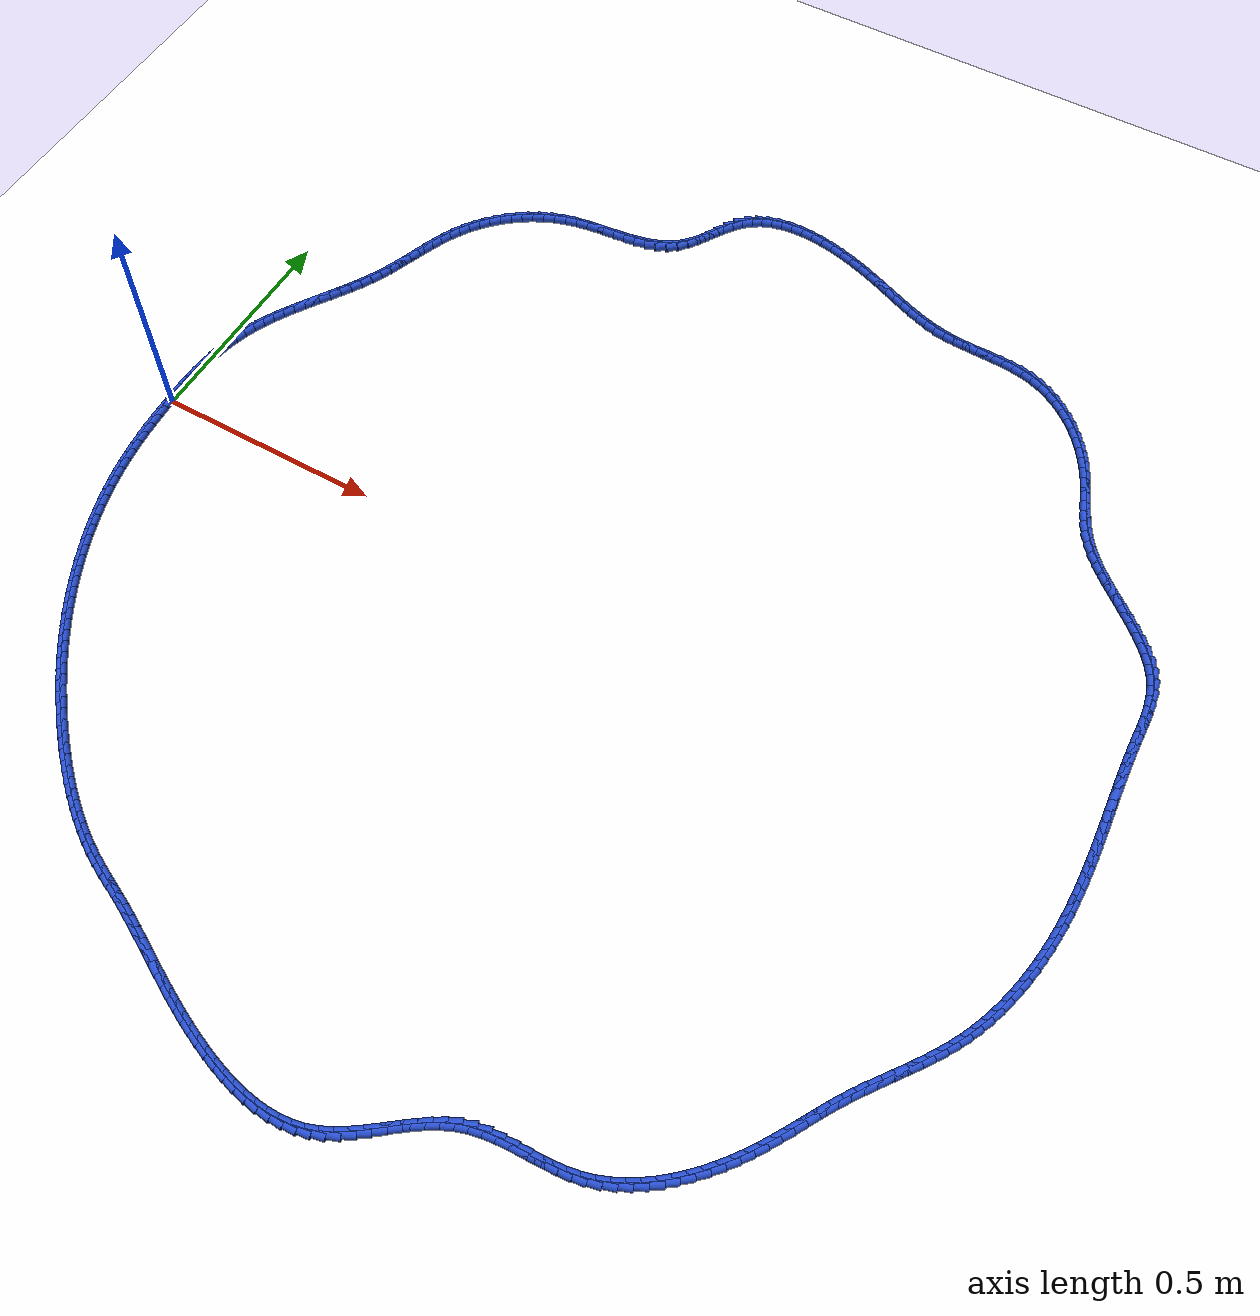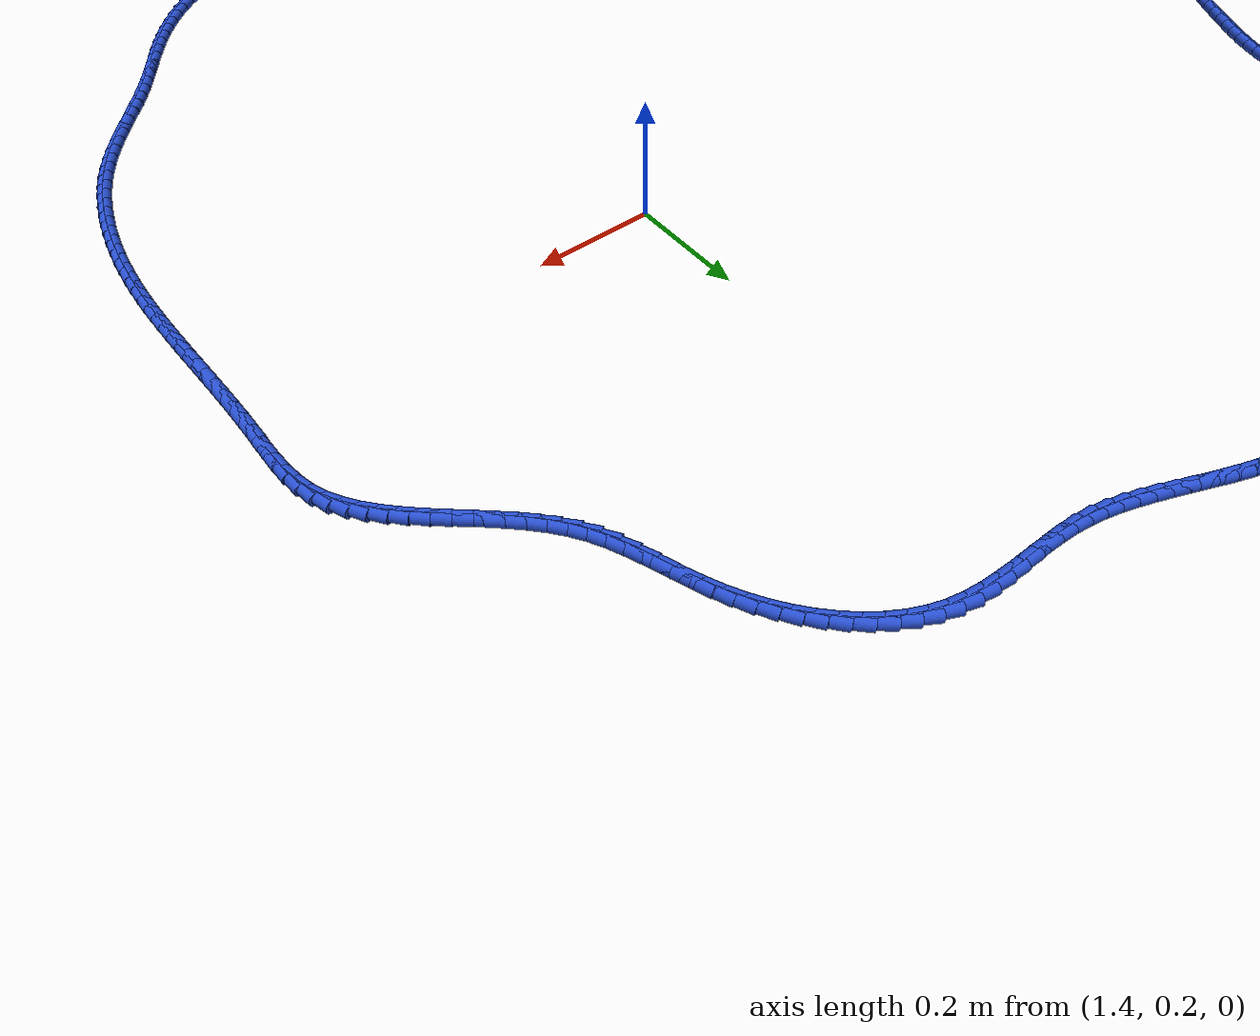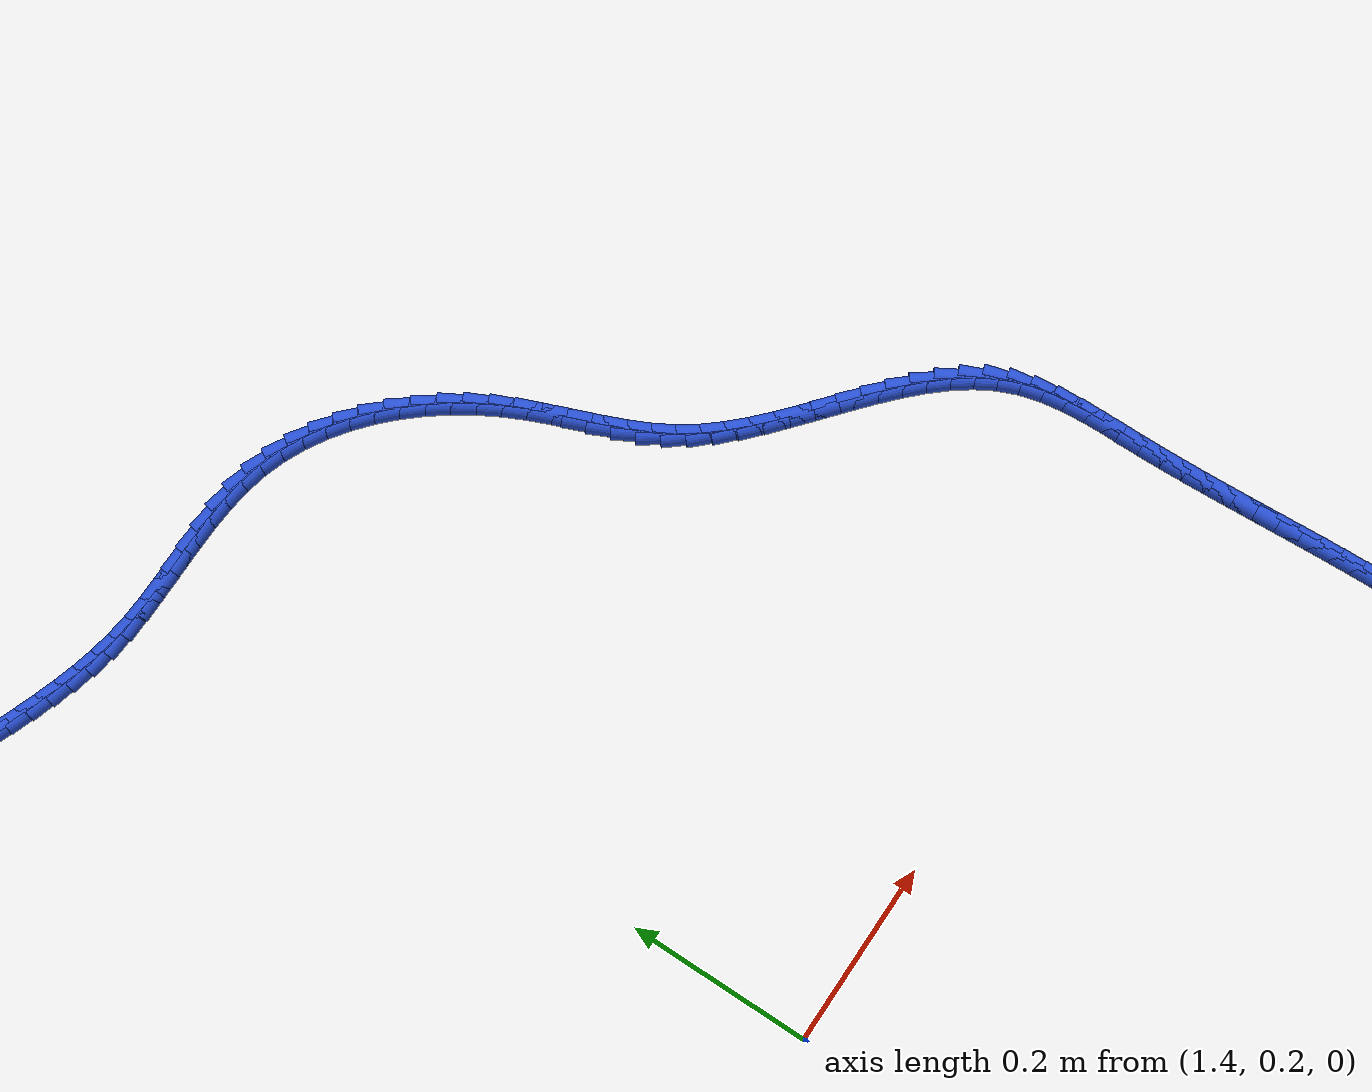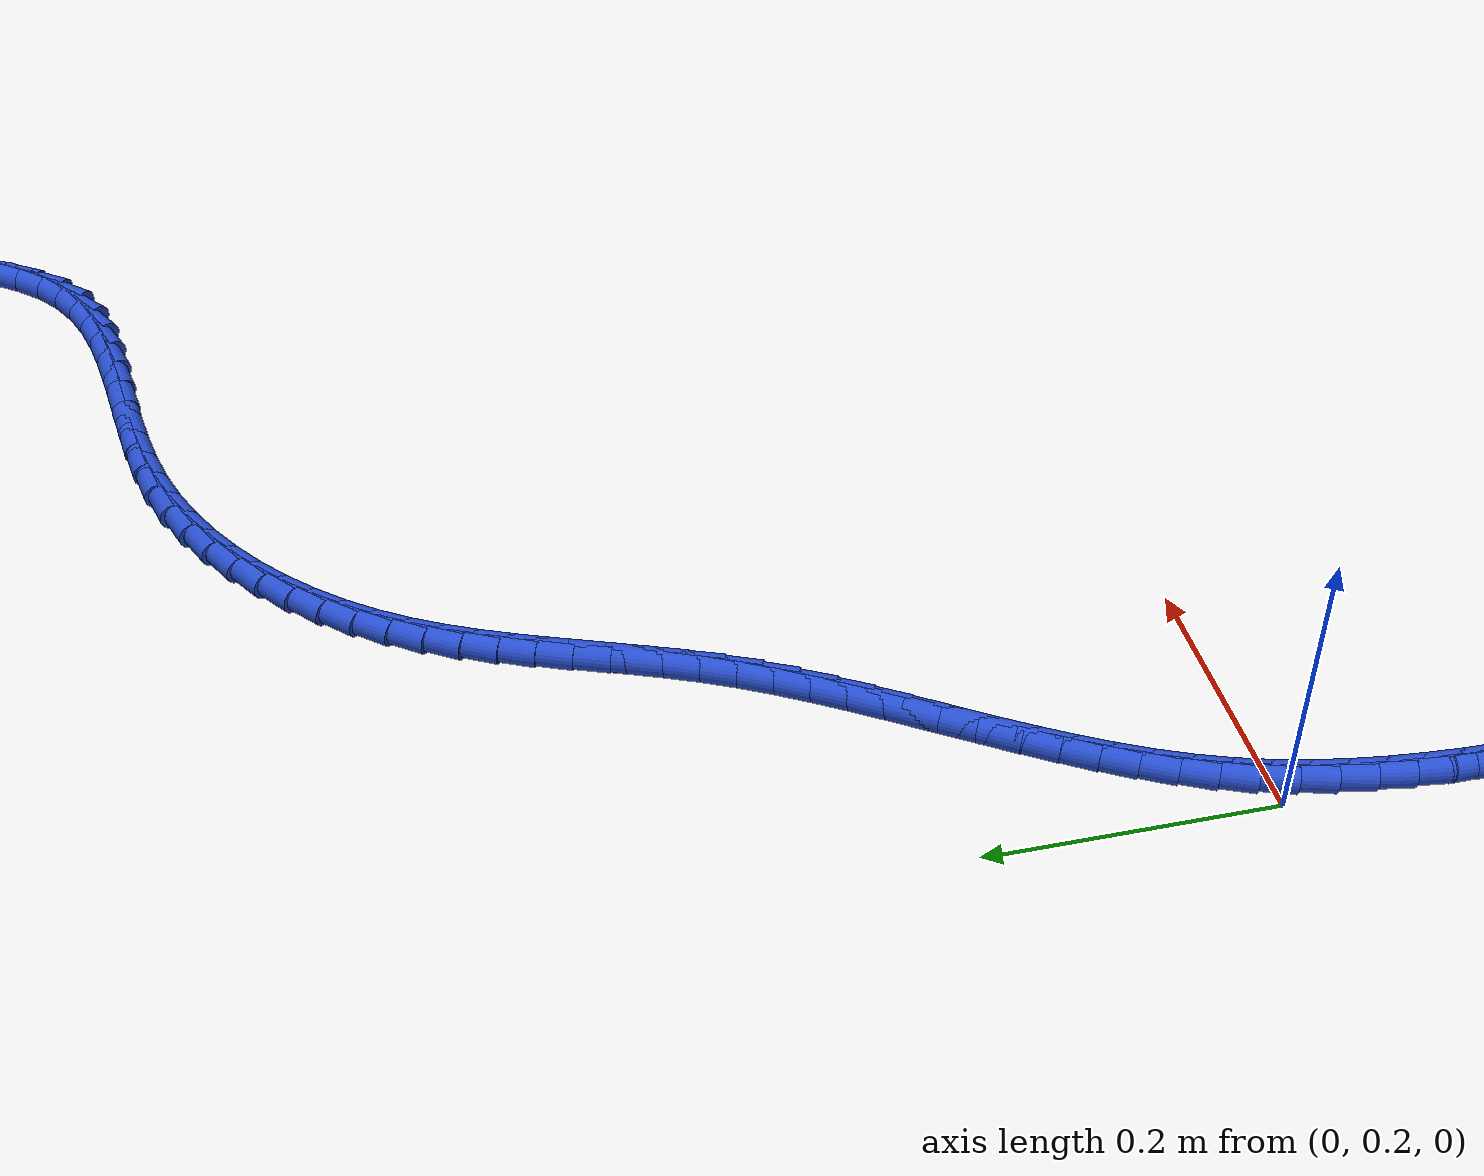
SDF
<sdf version="1.6">
 <world name="default">
  <light name="sun" type="directional">
   <pose>0 0 10 0 -0 0</pose>
   <diffuse>0.8 0.8 0.8 1</diffuse>
   <specular>0.2 0.2 0.2 1</specular>
   <attenuation>
    <range>1000</range>
    <constant>0.9</constant>
    <linear>0.01</linear>
    <quadratic>0.001</quadratic>
   </attenuation>
   <direction>-0.5 0.1 -0.9</direction>
  </light>
  <model name="ground_plane">
   <static>1</static>
   <link name="link">
    <collision name="collision">
     <geometry><plane><normal>0 0 1</normal><size>100 100</size></plane></geometry>
     <surface><friction><ode><mu>100</mu><mu2>50</mu2></ode></friction></surface>
    </collision>
    <visual name="visual">
     <cast_shadows>0</cast_shadows>
     <geometry><plane><normal>0 0 1</normal><size>100 100</size></plane></geometry>
     <material>
      <script><uri>file://media/materials/scripts/gazebo.material</uri><name>Gazebo/WhiteGlow</name></script>
     </material>
    </visual>
   </link>
  </model>
  <gravity>0 0 -9.8</gravity>
  <magnetic_field>6e-06 2.3e-05 -4.2e-05</magnetic_field>
  <atmosphere type="adiabatic"/>
  <physics name="default_physics" default="0" type="ode">
   <max_step_size>0.001</max_step_size>
   <real_time_factor>1</real_time_factor>
   <real_time_update_rate>1000</real_time_update_rate>
  </physics>
  <scene><ambient>0.4 0.4 0.4 1</ambient><background>0.7 0.7 0.7 1</background><shadows>1</shadows></scene>
  <spherical_coordinates>
   <surface_model>EARTH_WGS84</surface_model>
   <latitude_deg>0</latitude_deg>
   <longitude_deg>0</longitude_deg>
   <elevation>0</elevation>
   <heading_deg>0</heading_deg>
  </spherical_coordinates>
  <model name="line">
   <link name="link_0">
    <pose>-9.75781955236954e-18 6.938893903907228e-17 0.01 0 1.57 -1.555226522127229</pose>
    <collision name="collision">
     <geometry><cylinder><radius>0.01</radius><length>0.08</length></cylinder></geometry>
    </collision>
    <visual name="visual">
     <material>
      <script><name>Gazebo/Blue</name><uri>file://media/materials/scripts/gazebo.material</uri></script>
     </material>
     <geometry><cylinder><radius>0.01</radius><length>0.08</length></cylinder></geometry>
    </visual>
   </link>
   <link name="link_1">
    <pose>-0.00039559863322336566 0.025406013389314835 0.01 0 1.57 1.5662152106701432</pose>
    <collision name="collision">
     <geometry><cylinder><radius>0.01</radius><length>0.08</length></cylinder></geometry>
    </collision>
    <visual name="visual">
     <material>
      <script><name>Gazebo/Blue</name><uri>file://media/materials/scripts/gazebo.material</uri></script>
     </material>
     <geometry><cylinder><radius>0.01</radius><length>0.08</length></cylinder></geometry>
    </visual>
   </link>
   <link name="link_2">
    <pose>-0.0002790313549415987 0.050851005320326804 0.01 0 1.57 1.5414698510384934</pose>
    <collision name="collision">
     <geometry><cylinder><radius>0.01</radius><length>0.08</length></cylinder></geometry>
    </collision>
    <visual name="visual">
     <material>
      <script><name>Gazebo/Blue</name><uri>file://media/materials/scripts/gazebo.material</uri></script>
     </material>
     <geometry><cylinder><radius>0.01</radius><length>0.08</length></cylinder></geometry>
    </visual>
   </link>
   <link name="link_3">
    <pose>0.0004663814275333147 0.0762614597142718 0.01 0 1.57 1.5119396237090896</pose>
    <collision name="collision">
     <geometry><cylinder><radius>0.01</radius><length>0.08</length></cylinder></geometry>
    </collision>
    <visual name="visual">
     <material>
      <script><name>Gazebo/Blue</name><uri>file://media/materials/scripts/gazebo.material</uri></script>
     </material>
     <geometry><cylinder><radius>0.01</radius><length>0.08</length></cylinder></geometry>
    </visual>
   </link>
   <link name="link_4">
    <pose>0.0019573193068893966 0.10156386049238565 0.01 0 1.57 1.4773959164064112</pose>
    <collision name="collision">
     <geometry><cylinder><radius>0.01</radius><length>0.08</length></cylinder></geometry>
    </collision>
    <visual name="visual">
     <material>
      <script><name>Gazebo/Blue</name><uri>file://media/materials/scripts/gazebo.material</uri></script>
     </material>
     <geometry><cylinder><radius>0.01</radius><length>0.08</length></cylinder></geometry>
    </visual>
   </link>
   <link name="link_5">
    <pose>0.004310461875814669 0.12668469157590423 0.01 0 1.57 1.4375891591531478</pose>
    <collision name="collision">
     <geometry><cylinder><radius>0.01</radius><length>0.08</length></cylinder></geometry>
    </collision>
    <visual name="visual">
     <material>
      <script><name>Gazebo/Blue</name><uri>file://media/materials/scripts/gazebo.material</uri></script>
     </material>
     <geometry><cylinder><radius>0.01</radius><length>0.08</length></cylinder></geometry>
    </visual>
   </link>
   <link name="link_6">
    <pose>0.007642488726997158 0.15155043688606346 0.01 0 1.57 1.3922729450589235</pose>
    <collision name="collision">
     <geometry><cylinder><radius>0.01</radius><length>0.08</length></cylinder></geometry>
    </collision>
    <visual name="visual">
     <material>
      <script><name>Gazebo/Blue</name><uri>file://media/materials/scripts/gazebo.material</uri></script>
     </material>
     <geometry><cylinder><radius>0.01</radius><length>0.08</length></cylinder></geometry>
    </visual>
   </link>
   <link name="link_7">
    <pose>0.012070079453124882 0.176087580344099 0.01 0 1.57 1.3412371670263747</pose>
    <collision name="collision">
     <geometry><cylinder><radius>0.01</radius><length>0.08</length></cylinder></geometry>
    </collision>
    <visual name="visual">
     <material>
      <script><name>Gazebo/Blue</name><uri>file://media/materials/scripts/gazebo.material</uri></script>
     </material>
     <geometry><cylinder><radius>0.01</radius><length>0.08</length></cylinder></geometry>
    </visual>
   </link>
   <link name="link_8">
    <pose>0.017709913646885865 0.20022260587124688 0.01 0 1.57 1.2843515333578464</pose>
    <collision name="collision">
     <geometry><cylinder><radius>0.01</radius><length>0.08</length></cylinder></geometry>
    </collision>
    <visual name="visual">
     <material>
      <script><name>Gazebo/Blue</name><uri>file://media/materials/scripts/gazebo.material</uri></script>
     </material>
     <geometry><cylinder><radius>0.01</radius><length>0.08</length></cylinder></geometry>
    </visual>
   </link>
   <link name="link_9">
    <pose>0.02467867090096813 0.22388199738874281 0.01 0 1.57 1.2224601569509148</pose>
    <collision name="collision">
     <geometry><cylinder><radius>0.01</radius><length>0.08</length></cylinder></geometry>
    </collision>
    <visual name="visual">
     <material>
      <script><name>Gazebo/Blue</name><uri>file://media/materials/scripts/gazebo.material</uri></script>
     </material>
     <geometry><cylinder><radius>0.01</radius><length>0.08</length></cylinder></geometry>
    </visual>
   </link>
   <link name="link_10">
    <pose>0.033074374116202405 0.2470014780758318 0.01 0 1.57 1.1641607453258709</pose>
    <collision name="collision">
     <geometry><cylinder><radius>0.01</radius><length>0.08</length></cylinder></geometry>
    </collision>
    <visual name="visual">
     <material>
      <script><name>Gazebo/Blue</name><uri>file://media/materials/scripts/gazebo.material</uri></script>
     </material>
     <geometry><cylinder><radius>0.01</radius><length>0.08</length></cylinder></geometry>
    </visual>
   </link>
   <link name="link_11">
    <pose>0.04280979974318491 0.2696085097630729 0.01 0 1.57 1.1145856331024313</pose>
    <collision name="collision">
     <geometry><cylinder><radius>0.01</radius><length>0.08</length></cylinder></geometry>
    </collision>
    <visual name="visual">
     <material>
      <script><name>Gazebo/Blue</name><uri>file://media/materials/scripts/gazebo.material</uri></script>
     </material>
     <geometry><cylinder><radius>0.01</radius><length>0.08</length></cylinder></geometry>
    </visual>
   </link>
   <link name="link_12">
    <pose>0.053691697592667384 0.29178306131114834 0.01 0 1.57 1.0739037733721666</pose>
    <collision name="collision">
     <geometry><cylinder><radius>0.01</radius><length>0.08</length></cylinder></geometry>
    </collision>
    <visual name="visual">
     <material>
      <script><name>Gazebo/Blue</name><uri>file://media/materials/scripts/gazebo.material</uri></script>
     </material>
     <geometry><cylinder><radius>0.01</radius><length>0.08</length></cylinder></geometry>
    </visual>
   </link>
   <link name="link_13">
    <pose>0.06552556822395375 0.31360572024114053 0.01 0 1.57 1.0420394070131143</pose>
    <collision name="collision">
     <geometry><cylinder><radius>0.01</radius><length>0.08</length></cylinder></geometry>
    </collision>
    <visual name="visual">
     <material>
      <script><name>Gazebo/Blue</name><uri>file://media/materials/scripts/gazebo.material</uri></script>
     </material>
     <geometry><cylinder><radius>0.01</radius><length>0.08</length></cylinder></geometry>
    </visual>
   </link>
   <link name="link_14">
    <pose>0.07811691219634795 0.33515707407413164 0.01 0 1.57 1.0188252432628633</pose>
    <collision name="collision">
     <geometry><cylinder><radius>0.01</radius><length>0.08</length></cylinder></geometry>
    </collision>
    <visual name="visual">
     <material>
      <script><name>Gazebo/Blue</name><uri>file://media/materials/scripts/gazebo.material</uri></script>
     </material>
     <geometry><cylinder><radius>0.01</radius><length>0.08</length></cylinder></geometry>
    </visual>
   </link>
   <link name="link_15">
    <pose>0.0912712300691538 0.356517710331204 0.01 0 1.57 1.0040757195873862</pose>
    <collision name="collision">
     <geometry><cylinder><radius>0.01</radius><length>0.08</length></cylinder></geometry>
    </collision>
    <visual name="visual">
     <material>
      <script><name>Gazebo/Blue</name><uri>file://media/materials/scripts/gazebo.material</uri></script>
     </material>
     <geometry><cylinder><radius>0.01</radius><length>0.08</length></cylinder></geometry>
    </visual>
   </link>
   <link name="link_16">
    <pose>0.10479402240167532 0.37776821653343984 0.01 0 1.57 0.997636454147591</pose>
    <collision name="collision">
     <geometry><cylinder><radius>0.01</radius><length>0.08</length></cylinder></geometry>
    </collision>
    <visual name="visual">
     <material>
      <script><name>Gazebo/Blue</name><uri>file://media/materials/scripts/gazebo.material</uri></script>
     </material>
     <geometry><cylinder><radius>0.01</radius><length>0.08</length></cylinder></geometry>
    </visual>
   </link>
   <link name="link_17">
    <pose>0.11849078975321639 0.3989891802019214 0.01 0 1.57 0.9994129372983057</pose>
    <collision name="collision">
     <geometry><cylinder><radius>0.01</radius><length>0.08</length></cylinder></geometry>
    </collision>
    <visual name="visual">
     <material>
      <script><name>Gazebo/Blue</name><uri>file://media/materials/scripts/gazebo.material</uri></script>
     </material>
     <geometry><cylinder><radius>0.01</radius><length>0.08</length></cylinder></geometry>
    </visual>
   </link>
   <link name="link_18">
    <pose>0.1321670326830809 0.420261188857731 0.01 0 1.57 1.0093817251739032</pose>
    <collision name="collision">
     <geometry><cylinder><radius>0.01</radius><length>0.08</length></cylinder></geometry>
    </collision>
    <visual name="visual">
     <material>
      <script><name>Gazebo/Blue</name><uri>file://media/materials/scripts/gazebo.material</uri></script>
     </material>
     <geometry><cylinder><radius>0.01</radius><length>0.08</length></cylinder></geometry>
    </visual>
   </link>
   <link name="link_19">
    <pose>0.1456282517505727 0.44166483002195084 0.01 0 1.57 1.02758607794205</pose>
    <collision name="collision">
     <geometry><cylinder><radius>0.01</radius><length>0.08</length></cylinder></geometry>
    </collision>
    <visual name="visual">
     <material>
      <script><name>Gazebo/Blue</name><uri>file://media/materials/scripts/gazebo.material</uri></script>
     </material>
     <geometry><cylinder><radius>0.01</radius><length>0.08</length></cylinder></geometry>
    </visual>
   </link>
   <link name="link_20">
    <pose>0.1586799475149958 0.46328069121566323 0.01 0 1.57 1.0541161708580578</pose>
    <collision name="collision">
     <geometry><cylinder><radius>0.01</radius><length>0.08</length></cylinder></geometry>
    </collision>
    <visual name="visual">
     <material>
      <script><name>Gazebo/Blue</name><uri>file://media/materials/scripts/gazebo.material</uri></script>
     </material>
     <geometry><cylinder><radius>0.01</radius><length>0.08</length></cylinder></geometry>
    </visual>
   </link>
   <link name="link_21">
    <pose>0.17112762053565417 0.4851893599599505 0.01 0 1.57 1.08907243411517</pose>
    <collision name="collision">
     <geometry><cylinder><radius>0.01</radius><length>0.08</length></cylinder></geometry>
    </collision>
    <visual name="visual">
     <material>
      <script><name>Gazebo/Blue</name><uri>file://media/materials/scripts/gazebo.material</uri></script>
     </material>
     <geometry><cylinder><radius>0.01</radius><length>0.08</length></cylinder></geometry>
    </visual>
   </link>
   <link name="link_22">
    <pose>0.1827767713718516 0.5074714237758948 0.01 0 1.57 1.1322343189053872</pose>
    <collision name="collision">
     <geometry><cylinder><radius>0.01</radius><length>0.08</length></cylinder></geometry>
    </collision>
    <visual name="visual">
     <material>
      <script><name>Gazebo/Blue</name><uri>file://media/materials/scripts/gazebo.material</uri></script>
     </material>
     <geometry><cylinder><radius>0.01</radius><length>0.08</length></cylinder></geometry>
    </visual>
   </link>
   <link name="link_23">
    <pose>0.1934391950599923 0.5302045901730246 0.01 0 1.57 1.174004672617836</pose>
    <collision name="collision">
     <geometry><cylinder><radius>0.01</radius><length>0.08</length></cylinder></geometry>
    </collision>
    <visual name="visual">
     <material>
      <script><name>Gazebo/Blue</name><uri>file://media/materials/scripts/gazebo.material</uri></script>
     </material>
     <geometry><cylinder><radius>0.01</radius><length>0.08</length></cylinder></geometry>
    </visual>
   </link>
   <link name="link_24">
    <pose>0.20314457343079437 0.5533668734734867 0.01 0 1.57 1.2025626904053925</pose>
    <collision name="collision">
     <geometry><cylinder><radius>0.01</radius><length>0.08</length></cylinder></geometry>
    </collision>
    <visual name="visual">
     <material>
      <script><name>Gazebo/Blue</name><uri>file://media/materials/scripts/gazebo.material</uri></script>
     </material>
     <geometry><cylinder><radius>0.01</radius><length>0.08</length></cylinder></geometry>
    </visual>
   </link>
   <link name="link_25">
    <pose>0.21219102912794563 0.5768134640331893 0.01 0 1.57 1.2172318615747506</pose>
    <collision name="collision">
     <geometry><cylinder><radius>0.01</radius><length>0.08</length></cylinder></geometry>
    </collision>
    <visual name="visual">
     <material>
      <script><name>Gazebo/Blue</name><uri>file://media/materials/scripts/gazebo.material</uri></script>
     </material>
     <geometry><cylinder><radius>0.01</radius><length>0.08</length></cylinder></geometry>
    </visual>
   </link>
   <link name="link_26">
    <pose>0.22089322826653096 0.6003919828122044 0.01 0 1.57 1.2180556096643336</pose>
    <collision name="collision">
     <geometry><cylinder><radius>0.01</radius><length>0.08</length></cylinder></geometry>
    </collision>
    <visual name="visual">
     <material>
      <script><name>Gazebo/Blue</name><uri>file://media/materials/scripts/gazebo.material</uri></script>
     </material>
     <geometry><cylinder><radius>0.01</radius><length>0.08</length></cylinder></geometry>
    </visual>
   </link>
   <link name="link_27">
    <pose>0.22956583696163546 0.6239500507706031 0.01 0 1.57 1.2049880267554038</pose>
    <collision name="collision">
     <geometry><cylinder><radius>0.01</radius><length>0.08</length></cylinder></geometry>
    </collision>
    <visual name="visual">
     <material>
      <script><name>Gazebo/Blue</name><uri>file://media/materials/scripts/gazebo.material</uri></script>
     </material>
     <geometry><cylinder><radius>0.01</radius><length>0.08</length></cylinder></geometry>
    </visual>
   </link>
   <link name="link_28">
    <pose>0.2385235213283441 0.6473352888684566 0.01 0 1.57 1.1778881572873734</pose>
    <collision name="collision">
     <geometry><cylinder><radius>0.01</radius><length>0.08</length></cylinder></geometry>
    </collision>
    <visual name="visual">
     <material>
      <script><name>Gazebo/Blue</name><uri>file://media/materials/scripts/gazebo.material</uri></script>
     </material>
     <geometry><cylinder><radius>0.01</radius><length>0.08</length></cylinder></geometry>
    </visual>
   </link>
   <link name="link_29">
    <pose>0.24808094748174184 0.6703953180658363 0.01 0 1.57 1.1365950900157202</pose>
    <collision name="collision">
     <geometry><cylinder><radius>0.01</radius><length>0.08</length></cylinder></geometry>
    </collision>
    <visual name="visual">
     <material>
      <script><name>Gazebo/Blue</name><uri>file://media/materials/scripts/gazebo.material</uri></script>
     </material>
     <geometry><cylinder><radius>0.01</radius><length>0.08</length></cylinder></geometry>
    </visual>
   </link>
   <link name="link_30">
    <pose>0.25855278153691374 0.6929777593228135 0.01 0 1.57 1.0810900635389604</pose>
    <collision name="collision">
     <geometry><cylinder><radius>0.01</radius><length>0.08</length></cylinder></geometry>
    </collision>
    <visual name="visual">
     <material>
      <script><name>Gazebo/Blue</name><uri>file://media/materials/scripts/gazebo.material</uri></script>
     </material>
     <geometry><cylinder><radius>0.01</radius><length>0.08</length></cylinder></geometry>
    </visual>
   </link>
   <link name="link_31">
    <pose>0.27025368960894464 0.7149302335994593 0.01 0 1.57 1.012183170149901</pose>
    <collision name="collision">
     <geometry><cylinder><radius>0.01</radius><length>0.08</length></cylinder></geometry>
    </collision>
    <visual name="visual">
     <material>
      <script><name>Gazebo/Blue</name><uri>file://media/materials/scripts/gazebo.material</uri></script>
     </material>
     <geometry><cylinder><radius>0.01</radius><length>0.08</length></cylinder></geometry>
    </visual>
   </link>
   <link name="link_32">
    <pose>0.28348590255878614 0.7361011223159138 0.01 0 1.57 0.9378428382641664</pose>
    <collision name="collision">
     <geometry><cylinder><radius>0.01</radius><length>0.08</length></cylinder></geometry>
    </collision>
    <visual name="visual">
     <material>
      <script><name>Gazebo/Blue</name><uri>file://media/materials/scripts/gazebo.material</uri></script>
     </material>
     <geometry><cylinder><radius>0.01</radius><length>0.08</length></cylinder></geometry>
    </visual>
   </link>
   <link name="link_33">
    <pose>0.29834261948950414 0.7563515899286132 0.01 0 1.57 0.863908384403866</pose>
    <collision name="collision">
     <geometry><cylinder><radius>0.01</radius><length>0.08</length></cylinder></geometry>
    </collision>
    <visual name="visual">
     <material>
      <script><name>Gazebo/Blue</name><uri>file://media/materials/scripts/gazebo.material</uri></script>
     </material>
     <geometry><cylinder><radius>0.01</radius><length>0.08</length></cylinder></geometry>
    </visual>
   </link>
   <link name="link_34">
    <pose>0.31474350848996974 0.7755534129334037 0.01 0 1.57 0.7900186222673263</pose>
    <collision name="collision">
     <geometry><cylinder><radius>0.01</radius><length>0.08</length></cylinder></geometry>
    </collision>
    <visual name="visual">
     <material>
      <script><name>Gazebo/Blue</name><uri>file://media/materials/scripts/gazebo.material</uri></script>
     </material>
     <geometry><cylinder><radius>0.01</radius><length>0.08</length></cylinder></geometry>
    </visual>
   </link>
   <link name="link_35">
    <pose>0.33260297974181097 0.793578689365883 0.01 0 1.57 0.715653173320533</pose>
    <collision name="collision">
     <geometry><cylinder><radius>0.01</radius><length>0.08</length></cylinder></geometry>
    </collision>
    <visual name="visual">
     <material>
      <script><name>Gazebo/Blue</name><uri>file://media/materials/scripts/gazebo.material</uri></script>
     </material>
     <geometry><cylinder><radius>0.01</radius><length>0.08</length></cylinder></geometry>
    </visual>
   </link>
   <link name="link_36">
    <pose>0.35183544342665624 0.8102995172616478 0.01 0 1.57 0.6403303066077641</pose>
    <collision name="collision">
     <geometry><cylinder><radius>0.01</radius><length>0.08</length></cylinder></geometry>
    </collision>
    <visual name="visual">
     <material>
      <script><name>Gazebo/Blue</name><uri>file://media/materials/scripts/gazebo.material</uri></script>
     </material>
     <geometry><cylinder><radius>0.01</radius><length>0.08</length></cylinder></geometry>
    </visual>
   </link>
   <link name="link_37">
    <pose>0.37235530972613334 0.8255879946562947 0.01 0 1.57 0.5636212650688873</pose>
    <collision name="collision">
     <geometry><cylinder><radius>0.01</radius><length>0.08</length></cylinder></geometry>
    </collision>
    <visual name="visual">
     <material>
      <script><name>Gazebo/Blue</name><uri>file://media/materials/scripts/gazebo.material</uri></script>
     </material>
     <geometry><cylinder><radius>0.01</radius><length>0.08</length></cylinder></geometry>
    </visual>
   </link>
   <link name="link_38">
    <pose>0.3940769888218705 0.8393162195854211 0.01 0 1.57 0.48516763553434245</pose>
    <collision name="collision">
     <geometry><cylinder><radius>0.01</radius><length>0.08</length></cylinder></geometry>
    </collision>
    <visual name="visual">
     <material>
      <script><name>Gazebo/Blue</name><uri>file://media/materials/scripts/gazebo.material</uri></script>
     </material>
     <geometry><cylinder><radius>0.01</radius><length>0.08</length></cylinder></geometry>
    </visual>
   </link>
   <link name="link_39">
    <pose>0.41691489089549566 0.8513562900846238 0.01 0 1.57 0.4047021194049791</pose>
    <collision name="collision">
     <geometry><cylinder><radius>0.01</radius><length>0.08</length></cylinder></geometry>
    </collision>
    <visual name="visual">
     <material>
      <script><name>Gazebo/Blue</name><uri>file://media/materials/scripts/gazebo.material</uri></script>
     </material>
     <geometry><cylinder><radius>0.01</radius><length>0.08</length></cylinder></geometry>
    </visual>
   </link>
   <link name="link_40">
    <pose>0.44078342612863686 0.8615803041894994 0.01 0 1.57 0.3220719810025077</pose>
    <collision name="collision">
     <geometry><cylinder><radius>0.01</radius><length>0.08</length></cylinder></geometry>
    </collision>
    <visual name="visual">
     <material>
      <script><name>Gazebo/Blue</name><uri>file://media/materials/scripts/gazebo.material</uri></script>
     </material>
     <geometry><cylinder><radius>0.01</radius><length>0.08</length></cylinder></geometry>
    </visual>
   </link>
   <link name="link_41">
    <pose>0.4655970047029224 0.8698603599356453 0.01 0 1.57 0.2394755983449123</pose>
    <collision name="collision">
     <geometry><cylinder><radius>0.01</radius><length>0.08</length></cylinder></geometry>
    </collision>
    <visual name="visual">
     <material>
      <script><name>Gazebo/Blue</name><uri>file://media/materials/scripts/gazebo.material</uri></script>
     </material>
     <geometry><cylinder><radius>0.01</radius><length>0.08</length></cylinder></geometry>
    </visual>
   </link>
   <link name="link_42">
    <pose>0.49125258380330555 0.8761244509600482 0.01 0 1.57 0.1733927424901768</pose>
    <collision name="collision">
     <geometry><cylinder><radius>0.01</radius><length>0.08</length></cylinder></geometry>
    </collision>
    <visual name="visual">
     <material>
      <script><name>Gazebo/Blue</name><uri>file://media/materials/scripts/gazebo.material</uri></script>
     </material>
     <geometry><cylinder><radius>0.01</radius><length>0.08</length></cylinder></geometry>
    </visual>
   </link>
   <link name="link_43">
    <pose>0.51751480769111 0.8807243210771437 0.01 0 1.57 0.1302774589940562</pose>
    <collision name="collision">
     <geometry><cylinder><radius>0.01</radius><length>0.08</length></cylinder></geometry>
    </collision>
    <visual name="visual">
     <material>
      <script><name>Gazebo/Blue</name><uri>file://media/materials/scripts/gazebo.material</uri></script>
     </material>
     <geometry><cylinder><radius>0.01</radius><length>0.08</length></cylinder></geometry>
    </visual>
   </link>
   <link name="link_44">
    <pose>0.5440876913001884 0.8842058877887901 0.01 0 1.57 0.10902416511089205</pose>
    <collision name="collision">
     <geometry><cylinder><radius>0.01</radius><length>0.08</length></cylinder></geometry>
    </collision>
    <visual name="visual">
     <material>
      <script><name>Gazebo/Blue</name><uri>file://media/materials/scripts/gazebo.material</uri></script>
     </material>
     <geometry><cylinder><radius>0.01</radius><length>0.08</length></cylinder></geometry>
    </visual>
   </link>
   <link name="link_45">
    <pose>0.5706749339762863 0.8871160793107825 0.01 0 1.57 0.10926509526614214</pose>
    <collision name="collision">
     <geometry><cylinder><radius>0.01</radius><length>0.08</length></cylinder></geometry>
    </collision>
    <visual name="visual">
     <material>
      <script><name>Gazebo/Blue</name><uri>file://media/materials/scripts/gazebo.material</uri></script>
     </material>
     <geometry><cylinder><radius>0.01</radius><length>0.08</length></cylinder></geometry>
    </visual>
   </link>
   <link name="link_46">
    <pose>0.5969802350651494 0.8900018238589151 0.01 0 1.57 0.13170938318355405</pose>
    <collision name="collision">
     <geometry><cylinder><radius>0.01</radius><length>0.08</length></cylinder></geometry>
    </collision>
    <visual name="visual">
     <material>
      <script><name>Gazebo/Blue</name><uri>file://media/materials/scripts/gazebo.material</uri></script>
     </material>
     <geometry><cylinder><radius>0.01</radius><length>0.08</length></cylinder></geometry>
    </visual>
   </link>
   <link name="link_47">
    <pose>0.6227072939125249 0.8934100496489844 0.01 0 1.57 0.1782559398895576</pose>
    <collision name="collision">
     <geometry><cylinder><radius>0.01</radius><length>0.08</length></cylinder></geometry>
    </collision>
    <visual name="visual">
     <material>
      <script><name>Gazebo/Blue</name><uri>file://media/materials/scripts/gazebo.material</uri></script>
     </material>
     <geometry><cylinder><radius>0.01</radius><length>0.08</length></cylinder></geometry>
    </visual>
   </link>
   <link name="link_48">
    <pose>0.6475598098641581 0.8978876848967847 0.01 0 1.57 0.2518642389104652</pose>
    <collision name="collision">
     <geometry><cylinder><radius>0.01</radius><length>0.08</length></cylinder></geometry>
    </collision>
    <visual name="visual">
     <material>
      <script><name>Gazebo/Blue</name><uri>file://media/materials/scripts/gazebo.material</uri></script>
     </material>
     <geometry><cylinder><radius>0.01</radius><length>0.08</length></cylinder></geometry>
    </visual>
   </link>
   <link name="link_49">
    <pose>0.6712414822657947 0.9039816578181111 0.01 0 1.57 0.35587828829496043</pose>
    <collision name="collision">
     <geometry><cylinder><radius>0.01</radius><length>0.08</length></cylinder></geometry>
    </collision>
    <visual name="visual">
     <material>
      <script><name>Gazebo/Blue</name><uri>file://media/materials/scripts/gazebo.material</uri></script>
     </material>
     <geometry><cylinder><radius>0.01</radius><length>0.08</length></cylinder></geometry>
    </visual>
   </link>
   <link name="link_50">
    <pose>0.6934560104631813 0.9122388966287589 0.01 0 1.57 0.4922458240336488</pose>
    <collision name="collision">
     <geometry><cylinder><radius>0.01</radius><length>0.08</length></cylinder></geometry>
    </collision>
    <visual name="visual">
     <material>
      <script><name>Gazebo/Blue</name><uri>file://media/materials/scripts/gazebo.material</uri></script>
     </material>
     <geometry><cylinder><radius>0.01</radius><length>0.08</length></cylinder></geometry>
    </visual>
   </link>
   <link name="link_51">
    <pose>0.7139070938020636 0.9232063295445232 0.01 0 1.57 0.6583331237046401</pose>
    <collision name="collision">
     <geometry><cylinder><radius>0.01</radius><length>0.08</length></cylinder></geometry>
    </collision>
    <visual name="visual">
     <material>
      <script><name>Gazebo/Blue</name><uri>file://media/materials/scripts/gazebo.material</uri></script>
     </material>
     <geometry><cylinder><radius>0.01</radius><length>0.08</length></cylinder></geometry>
    </visual>
   </link>
   <link name="link_52">
    <pose>0.7322984339376766 0.9374308809552352 0.01 0 1.57 0.8297041908526335</pose>
    <collision name="collision">
     <geometry><cylinder><radius>0.01</radius><length>0.08</length></cylinder></geometry>
    </collision>
    <visual name="visual">
     <material>
      <script><name>Gazebo/Blue</name><uri>file://media/materials/scripts/gazebo.material</uri></script>
     </material>
     <geometry><cylinder><radius>0.01</radius><length>0.08</length></cylinder></geometry>
    </visual>
   </link>
   <link name="link_53">
    <pose>0.748517583552592 0.955154902470993 0.01 0 1.57 0.9474010024520524</pose>
    <collision name="collision">
     <geometry><cylinder><radius>0.01</radius><length>0.08</length></cylinder></geometry>
    </collision>
    <visual name="visual">
     <material>
      <script><name>Gazebo/Blue</name><uri>file://media/materials/scripts/gazebo.material</uri></script>
     </material>
     <geometry><cylinder><radius>0.01</radius><length>0.08</length></cylinder></geometry>
    </visual>
   </link>
   <link name="link_54">
    <pose>0.7631368565161908 0.9754863510719597 0.01 0 1.57 1.0076916436943326</pose>
    <collision name="collision">
     <geometry><cylinder><radius>0.01</radius><length>0.08</length></cylinder></geometry>
    </collision>
    <visual name="visual">
     <material>
      <script><name>Gazebo/Blue</name><uri>file://media/materials/scripts/gazebo.material</uri></script>
     </material>
     <geometry><cylinder><radius>0.01</radius><length>0.08</length></cylinder></geometry>
    </visual>
   </link>
   <link name="link_55">
    <pose>0.7768879569372612 0.9972691333874147 0.01 0 1.57 1.0182168545617885</pose>
    <collision name="collision">
     <geometry><cylinder><radius>0.01</radius><length>0.08</length></cylinder></geometry>
    </collision>
    <visual name="visual">
     <material>
      <script><name>Gazebo/Blue</name><uri>file://media/materials/scripts/gazebo.material</uri></script>
     </material>
     <geometry><cylinder><radius>0.01</radius><length>0.08</length></cylinder></geometry>
    </visual>
   </link>
   <link name="link_56">
    <pose>0.7905025889245912 1.0193471560466383 0.01 0 1.57 0.9806729369856424</pose>
    <collision name="collision">
     <geometry><cylinder><radius>0.01</radius><length>0.08</length></cylinder></geometry>
    </collision>
    <visual name="visual">
     <material>
      <script><name>Gazebo/Blue</name><uri>file://media/materials/scripts/gazebo.material</uri></script>
     </material>
     <geometry><cylinder><radius>0.01</radius><length>0.08</length></cylinder></geometry>
    </visual>
   </link>
   <link name="link_57">
    <pose>0.8047124565869689 1.0405643256789099 0.01 0 1.57 0.8904711648474194</pose>
    <collision name="collision">
     <geometry><cylinder><radius>0.01</radius><length>0.08</length></cylinder></geometry>
    </collision>
    <visual name="visual">
     <material>
      <script><name>Gazebo/Blue</name><uri>file://media/materials/scripts/gazebo.material</uri></script>
     </material>
     <geometry><cylinder><radius>0.01</radius><length>0.08</length></cylinder></geometry>
    </visual>
   </link>
   <link name="link_58">
    <pose>0.8202492640331822 1.0597645489135092 0.01 0 1.57 0.7402906083962236</pose>
    <collision name="collision">
     <geometry><cylinder><radius>0.01</radius><length>0.08</length></cylinder></geometry>
    </collision>
    <visual name="visual">
     <material>
      <script><name>Gazebo/Blue</name><uri>file://media/materials/scripts/gazebo.material</uri></script>
     </material>
     <geometry><cylinder><radius>0.01</radius><length>0.08</length></cylinder></geometry>
    </visual>
   </link>
   <link name="link_59">
    <pose>0.8378237053422839 1.0758209551977098 0.01 0 1.57 0.5612397379594953</pose>
    <collision name="collision">
     <geometry><cylinder><radius>0.01</radius><length>0.08</length></cylinder></geometry>
    </collision>
    <visual name="visual">
     <material>
      <script><name>Gazebo/Blue</name><uri>file://media/materials/scripts/gazebo.material</uri></script>
     </material>
     <geometry><cylinder><radius>0.01</radius><length>0.08</length></cylinder></geometry>
    </visual>
   </link>
   <link name="link_60">
    <pose>0.8576558977343933 1.0882890165761303 0.01 0 1.57 0.3960996355462212</pose>
    <collision name="collision">
     <geometry><cylinder><radius>0.01</radius><length>0.08</length></cylinder></geometry>
    </collision>
    <visual name="visual">
     <material>
      <script><name>Gazebo/Blue</name><uri>file://media/materials/scripts/gazebo.material</uri></script>
     </material>
     <geometry><cylinder><radius>0.01</radius><length>0.08</length></cylinder></geometry>
    </visual>
   </link>
   <link name="link_61">
    <pose>0.8794712653191094 1.09741227297873 0.01 0 1.57 0.2520472753981292</pose>
    <collision name="collision">
     <geometry><cylinder><radius>0.01</radius><length>0.08</length></cylinder></geometry>
    </collision>
    <visual name="visual">
     <material>
      <script><name>Gazebo/Blue</name><uri>file://media/materials/scripts/gazebo.material</uri></script>
     </material>
     <geometry><cylinder><radius>0.01</radius><length>0.08</length></cylinder></geometry>
    </visual>
   </link>
   <link name="link_62">
    <pose>0.9029733989079586 1.1034646322361195 0.01 0 1.57 0.1300392015710237</pose>
    <collision name="collision">
     <geometry><cylinder><radius>0.01</radius><length>0.08</length></cylinder></geometry>
    </collision>
    <visual name="visual">
     <material>
      <script><name>Gazebo/Blue</name><uri>file://media/materials/scripts/gazebo.material</uri></script>
     </material>
     <geometry><cylinder><radius>0.01</radius><length>0.08</length></cylinder></geometry>
    </visual>
   </link>
   <link name="link_63">
    <pose>0.9278658893124679 1.1067200021789112 0.01 0 1.57 0.028172184098085695</pose>
    <collision name="collision">
     <geometry><cylinder><radius>0.01</radius><length>0.08</length></cylinder></geometry>
    </collision>
    <visual name="visual">
     <material>
      <script><name>Gazebo/Blue</name><uri>file://media/materials/scripts/gazebo.material</uri></script>
     </material>
     <geometry><cylinder><radius>0.01</radius><length>0.08</length></cylinder></geometry>
    </visual>
   </link>
   <link name="link_64">
    <pose>0.9538523273441644 1.1074522906377164 0.01 0 1.57 -0.05657362152343595</pose>
    <collision name="collision">
     <geometry><cylinder><radius>0.01</radius><length>0.08</length></cylinder></geometry>
    </collision>
    <visual name="visual">
     <material>
      <script><name>Gazebo/Blue</name><uri>file://media/materials/scripts/gazebo.material</uri></script>
     </material>
     <geometry><cylinder><radius>0.01</radius><length>0.08</length></cylinder></geometry>
    </visual>
   </link>
   <link name="link_65">
    <pose>0.9806363038145751 1.1059354054431472 0.01 0 1.57 -0.1272953910247561</pose>
    <collision name="collision">
     <geometry><cylinder><radius>0.01</radius><length>0.08</length></cylinder></geometry>
    </collision>
    <visual name="visual">
     <material>
      <script><name>Gazebo/Blue</name><uri>file://media/materials/scripts/gazebo.material</uri></script>
     </material>
     <geometry><cylinder><radius>0.01</radius><length>0.08</length></cylinder></geometry>
    </visual>
   </link>
   <link name="link_66">
    <pose>1.007921409535227 1.1024432544258158 0.01 0 1.57 -0.18672397546534408</pose>
    <collision name="collision">
     <geometry><cylinder><radius>0.01</radius><length>0.08</length></cylinder></geometry>
    </collision>
    <visual name="visual">
     <material>
      <script><name>Gazebo/Blue</name><uri>file://media/materials/scripts/gazebo.material</uri></script>
     </material>
     <geometry><cylinder><radius>0.01</radius><length>0.08</length></cylinder></geometry>
    </visual>
   </link>
   <link name="link_67">
    <pose>1.0354112353176461 1.097249745416333 0.01 0 1.57 -0.23711140964221325</pose>
    <collision name="collision">
     <geometry><cylinder><radius>0.01</radius><length>0.08</length></cylinder></geometry>
    </collision>
    <visual name="visual">
     <material>
      <script><name>Gazebo/Blue</name><uri>file://media/materials/scripts/gazebo.material</uri></script>
     </material>
     <geometry><cylinder><radius>0.01</radius><length>0.08</length></cylinder></geometry>
    </visual>
   </link>
   <link name="link_68">
    <pose>1.0628093719733607 1.0906287862453112 0.01 0 1.57 -0.2802615138921303</pose>
    <collision name="collision">
     <geometry><cylinder><radius>0.01</radius><length>0.08</length></cylinder></geometry>
    </collision>
    <visual name="visual">
     <material>
      <script><name>Gazebo/Blue</name><uri>file://media/materials/scripts/gazebo.material</uri></script>
     </material>
     <geometry><cylinder><radius>0.01</radius><length>0.08</length></cylinder></geometry>
    </visual>
   </link>
   <link name="link_69">
    <pose>1.0898194103138965 1.082854284743362 0.01 0 1.57 -0.3176067651948003</pose>
    <collision name="collision">
     <geometry><cylinder><radius>0.01</radius><length>0.08</length></cylinder></geometry>
    </collision>
    <visual name="visual">
     <material>
      <script><name>Gazebo/Blue</name><uri>file://media/materials/scripts/gazebo.material</uri></script>
     </material>
     <geometry><cylinder><radius>0.01</radius><length>0.08</length></cylinder></geometry>
    </visual>
   </link>
   <link name="link_70">
    <pose>1.1161449455556485 1.0742001481301984 0.01 0 1.57 -0.34963420881714574</pose>
    <collision name="collision">
     <geometry><cylinder><radius>0.01</radius><length>0.08</length></cylinder></geometry>
    </collision>
    <visual name="visual">
     <material>
      <script><name>Gazebo/Blue</name><uri>file://media/materials/scripts/gazebo.material</uri></script>
     </material>
     <geometry><cylinder><radius>0.01</radius><length>0.08</length></cylinder></geometry>
    </visual>
   </link>
   <link name="link_71">
    <pose>1.1415730427100592 1.064928707435475 0.01 0 1.57 -0.3742459113744424</pose>
    <collision name="collision">
     <geometry><cylinder><radius>0.01</radius><length>0.08</length></cylinder></geometry>
    </collision>
    <visual name="visual">
     <material>
      <script><name>Gazebo/Blue</name><uri>file://media/materials/scripts/gazebo.material</uri></script>
     </material>
     <geometry><cylinder><radius>0.01</radius><length>0.08</length></cylinder></geometry>
    </visual>
   </link>
   <link name="link_72">
    <pose>1.1661878675069677 1.0552610896295747 0.01 0 1.57 -0.3902260509429083</pose>
    <collision name="collision">
     <geometry><cylinder><radius>0.01</radius><length>0.08</length></cylinder></geometry>
    </collision>
    <visual name="visual">
     <material>
      <script><name>Gazebo/Blue</name><uri>file://media/materials/scripts/gazebo.material</uri></script>
     </material>
     <geometry><cylinder><radius>0.01</radius><length>0.08</length></cylinder></geometry>
    </visual>
   </link>
   <link name="link_73">
    <pose>1.1901396593611218 1.0454092581101886 0.01 0 1.57 -0.3968916456069579</pose>
    <collision name="collision">
     <geometry><cylinder><radius>0.01</radius><length>0.08</length></cylinder></geometry>
    </collision>
    <visual name="visual">
     <material>
      <script><name>Gazebo/Blue</name><uri>file://media/materials/scripts/gazebo.material</uri></script>
     </material>
     <geometry><cylinder><radius>0.01</radius><length>0.08</length></cylinder></geometry>
    </visual>
   </link>
   <link name="link_74">
    <pose>1.2135786576872707 1.0355851762750101 0.01 0 1.57 -0.39365272293426523</pose>
    <collision name="collision">
     <geometry><cylinder><radius>0.01</radius><length>0.08</length></cylinder></geometry>
    </collision>
    <visual name="visual">
     <material>
      <script><name>Gazebo/Blue</name><uri>file://media/materials/scripts/gazebo.material</uri></script>
     </material>
     <geometry><cylinder><radius>0.01</radius><length>0.08</length></cylinder></geometry>
    </visual>
   </link>
   <link name="link_75">
    <pose>1.2366551019001624 1.0260008075217302 0.01 0 1.57 -0.3800176555319</pose>
    <collision name="collision">
     <geometry><cylinder><radius>0.01</radius><length>0.08</length></cylinder></geometry>
    </collision>
    <visual name="visual">
     <material>
      <script><name>Gazebo/Blue</name><uri>file://media/materials/scripts/gazebo.material</uri></script>
     </material>
     <geometry><cylinder><radius>0.01</radius><length>0.08</length></cylinder></geometry>
    </visual>
   </link>
   <link name="link_76">
    <pose>1.2595192314145456 1.0168681152480417 0.01 0 1.57 -0.3556250150488615</pose>
    <collision name="collision">
     <geometry><cylinder><radius>0.01</radius><length>0.08</length></cylinder></geometry>
    </collision>
    <visual name="visual">
     <material>
      <script><name>Gazebo/Blue</name><uri>file://media/materials/scripts/gazebo.material</uri></script>
     </material>
     <geometry><cylinder><radius>0.01</radius><length>0.08</length></cylinder></geometry>
    </visual>
   </link>
   <link name="link_77">
    <pose>1.2823212856451687 1.0083990628516366 0.01 0 1.57 -0.3203098907652909</pose>
    <collision name="collision">
     <geometry><cylinder><radius>0.01</radius><length>0.08</length></cylinder></geometry>
    </collision>
    <visual name="visual">
     <material>
      <script><name>Gazebo/Blue</name><uri>file://media/materials/scripts/gazebo.material</uri></script>
     </material>
     <geometry><cylinder><radius>0.01</radius><length>0.08</length></cylinder></geometry>
    </visual>
   </link>
   <link name="link_78">
    <pose>1.3052115040067798 1.0008056137302064 0.01 0 1.57 -0.27420581645033437</pose>
    <collision name="collision">
     <geometry><cylinder><radius>0.01</radius><length>0.08</length></cylinder></geometry>
    </collision>
    <visual name="visual">
     <material>
      <script><name>Gazebo/Blue</name><uri>file://media/materials/scripts/gazebo.material</uri></script>
     </material>
     <geometry><cylinder><radius>0.01</radius><length>0.08</length></cylinder></geometry>
    </visual>
   </link>
   <link name="link_79">
    <pose>1.3283401259141272 0.9942997312814437 0.01 0 1.57 -0.21787027960239017</pose>
    <collision name="collision">
     <geometry><cylinder><radius>0.01</radius><length>0.08</length></cylinder></geometry>
    </collision>
    <visual name="visual">
     <material>
      <script><name>Gazebo/Blue</name><uri>file://media/materials/scripts/gazebo.material</uri></script>
     </material>
     <geometry><cylinder><radius>0.01</radius><length>0.08</length></cylinder></geometry>
    </visual>
   </link>
   <link name="link_80">
    <pose>1.35185739078196 0.9890933789030405 0.01 0 1.57 -0.15258427737276412</pose>
    <collision name="collision">
     <geometry><cylinder><radius>0.01</radius><length>0.08</length></cylinder></geometry>
    </collision>
    <visual name="visual">
     <material>
      <script><name>Gazebo/Blue</name><uri>file://media/materials/scripts/gazebo.material</uri></script>
     </material>
     <geometry><cylinder><radius>0.01</radius><length>0.08</length></cylinder></geometry>
    </visual>
   </link>
   <link name="link_81">
    <pose>1.3759116846736923 0.9853943200803523 0.01 0 1.57 -0.09104105246855446</pose>
    <collision name="collision">
     <geometry><cylinder><radius>0.01</radius><length>0.08</length></cylinder></geometry>
    </collision>
    <visual name="visual">
     <material>
      <script><name>Gazebo/Blue</name><uri>file://media/materials/scripts/gazebo.material</uri></script>
     </material>
     <geometry><cylinder><radius>0.01</radius><length>0.08</length></cylinder></geometry>
    </visual>
   </link>
   <link name="link_82">
    <pose>1.400534922306277 0.9831463805142846 0.01 0 1.57 -0.05063932183384074</pose>
    <collision name="collision">
     <geometry><cylinder><radius>0.01</radius><length>0.08</length></cylinder></geometry>
    </collision>
    <visual name="visual">
     <material>
      <script><name>Gazebo/Blue</name><uri>file://media/materials/scripts/gazebo.material</uri></script>
     </material>
     <geometry><cylinder><radius>0.01</radius><length>0.08</length></cylinder></geometry>
    </visual>
   </link>
   <link name="link_83">
    <pose>1.425575390376145 0.9818772631908301 0.01 0 1.57 -0.03159195191664703</pose>
    <collision name="collision">
     <geometry><cylinder><radius>0.01</radius><length>0.08</length></cylinder></geometry>
    </collision>
    <visual name="visual">
     <material>
      <script><name>Gazebo/Blue</name><uri>file://media/materials/scripts/gazebo.material</uri></script>
     </material>
     <geometry><cylinder><radius>0.01</radius><length>0.08</length></cylinder></geometry>
    </visual>
   </link>
   <link name="link_84">
    <pose>1.450865211971886 0.9810780424575064 0.01 0 1.57 -0.033027280614031415</pose>
    <collision name="collision">
     <geometry><cylinder><radius>0.01</radius><length>0.08</length></cylinder></geometry>
    </collision>
    <visual name="visual">
     <material>
      <script><name>Gazebo/Blue</name><uri>file://media/materials/scripts/gazebo.material</uri></script>
     </material>
     <geometry><cylinder><radius>0.01</radius><length>0.08</length></cylinder></geometry>
    </visual>
   </link>
   <link name="link_85">
    <pose>1.476236510182089 0.9802397926618301 0.01 0 1.57 -0.05476859028792677</pose>
    <collision name="collision">
     <geometry><cylinder><radius>0.01</radius><length>0.08</length></cylinder></geometry>
    </collision>
    <visual name="visual">
     <material>
      <script><name>Gazebo/Blue</name><uri>file://media/materials/scripts/gazebo.material</uri></script>
     </material>
     <geometry><cylinder><radius>0.01</radius><length>0.08</length></cylinder></geometry>
    </visual>
   </link>
   <link name="link_86">
    <pose>1.5015214080953452 0.9788535881513192 0.01 0 1.57 -0.09729566542460004</pose>
    <collision name="collision">
     <geometry><cylinder><radius>0.01</radius><length>0.08</length></cylinder></geometry>
    </collision>
    <visual name="visual">
     <material>
      <script><name>Gazebo/Blue</name><uri>file://media/materials/scripts/gazebo.material</uri></script>
     </material>
     <geometry><cylinder><radius>0.01</radius><length>0.08</length></cylinder></geometry>
    </visual>
   </link>
   <link name="link_87">
    <pose>1.5265520288002434 0.9764105032734904 0.01 0 1.57 -0.16148838562098314</pose>
    <collision name="collision">
     <geometry><cylinder><radius>0.01</radius><length>0.08</length></cylinder></geometry>
    </collision>
    <visual name="visual">
     <material>
      <script><name>Gazebo/Blue</name><uri>file://media/materials/scripts/gazebo.material</uri></script>
     </material>
     <geometry><cylinder><radius>0.01</radius><length>0.08</length></cylinder></geometry>
    </visual>
   </link>
   <link name="link_88">
    <pose>1.5511604953853733 0.972401612375861 0.01 0 1.57 -0.2480724559041302</pose>
    <collision name="collision">
     <geometry><cylinder><radius>0.01</radius><length>0.08</length></cylinder></geometry>
    </collision>
    <visual name="visual">
     <material>
      <script><name>Gazebo/Blue</name><uri>file://media/materials/scripts/gazebo.material</uri></script>
     </material>
     <geometry><cylinder><radius>0.01</radius><length>0.08</length></cylinder></geometry>
    </visual>
   </link>
   <link name="link_89">
    <pose>1.5751789309393256 0.9663179898059485 0.01 0 1.57 -0.35248880390387805</pose>
    <collision name="collision">
     <geometry><cylinder><radius>0.01</radius><length>0.08</length></cylinder></geometry>
    </collision>
    <visual name="visual">
     <material>
      <script><name>Gazebo/Blue</name><uri>file://media/materials/scripts/gazebo.material</uri></script>
     </material>
     <geometry><cylinder><radius>0.01</radius><length>0.08</length></cylinder></geometry>
    </visual>
   </link>
   <link name="link_90">
    <pose>1.5984519741683418 0.9577569661334764 0.01 0 1.57 -0.4546174491723738</pose>
    <collision name="collision">
     <geometry><cylinder><radius>0.01</radius><length>0.08</length></cylinder></geometry>
    </collision>
    <visual name="visual">
     <material>
      <script><name>Gazebo/Blue</name><uri>file://media/materials/scripts/gazebo.material</uri></script>
     </material>
     <geometry><cylinder><radius>0.01</radius><length>0.08</length></cylinder></geometry>
    </visual>
   </link>
   <link name="link_91">
    <pose>1.620880658964905 0.9467946608786438 0.01 0 1.57 -0.5489903803557981</pose>
    <collision name="collision">
     <geometry><cylinder><radius>0.01</radius><length>0.08</length></cylinder></geometry>
    </collision>
    <visual name="visual">
     <material>
      <script><name>Gazebo/Blue</name><uri>file://media/materials/scripts/gazebo.material</uri></script>
     </material>
     <geometry><cylinder><radius>0.01</radius><length>0.08</length></cylinder></geometry>
    </visual>
   </link>
   <link name="link_92">
    <pose>1.642381896474009 0.9336419896953775 0.01 0 1.57 -0.6360918759632034</pose>
    <collision name="collision">
     <geometry><cylinder><radius>0.01</radius><length>0.08</length></cylinder></geometry>
    </collision>
    <visual name="visual">
     <material>
      <script><name>Gazebo/Blue</name><uri>file://media/materials/scripts/gazebo.material</uri></script>
     </material>
     <geometry><cylinder><radius>0.01</radius><length>0.08</length></cylinder></geometry>
    </visual>
   </link>
   <link name="link_93">
    <pose>1.6628725987227213 0.9185098757263233 0.01 0 1.57 -0.7167293665847518</pose>
    <collision name="collision">
     <geometry><cylinder><radius>0.01</radius><length>0.08</length></cylinder></geometry>
    </collision>
    <visual name="visual">
     <material>
      <script><name>Gazebo/Blue</name><uri>file://media/materials/scripts/gazebo.material</uri></script>
     </material>
     <geometry><cylinder><radius>0.01</radius><length>0.08</length></cylinder></geometry>
    </visual>
   </link>
   <link name="link_94">
    <pose>1.6822696777381105 0.9016092421141275 0.01 0 1.57 -0.7918831160025479</pose>
    <collision name="collision">
     <geometry><cylinder><radius>0.01</radius><length>0.08</length></cylinder></geometry>
    </collision>
    <visual name="visual">
     <material>
      <script><name>Gazebo/Blue</name><uri>file://media/materials/scripts/gazebo.material</uri></script>
     </material>
     <geometry><cylinder><radius>0.01</radius><length>0.08</length></cylinder></geometry>
    </visual>
   </link>
   <link name="link_95">
    <pose>1.7004900455472451 0.8831510120014369 0.01 0 1.57 -0.8626086628195517</pose>
    <collision name="collision">
     <geometry><cylinder><radius>0.01</radius><length>0.08</length></cylinder></geometry>
    </collision>
    <visual name="visual">
     <material>
      <script><name>Gazebo/Blue</name><uri>file://media/materials/scripts/gazebo.material</uri></script>
     </material>
     <geometry><cylinder><radius>0.01</radius><length>0.08</length></cylinder></geometry>
    </visual>
   </link>
   <link name="link_96">
    <pose>1.7174506141771926 0.8633461085308975 0.01 0 1.57 -0.9299842853119031</pose>
    <collision name="collision">
     <geometry><cylinder><radius>0.01</radius><length>0.08</length></cylinder></geometry>
    </collision>
    <visual name="visual">
     <material>
      <script><name>Gazebo/Blue</name><uri>file://media/materials/scripts/gazebo.material</uri></script>
     </material>
     <geometry><cylinder><radius>0.01</radius><length>0.08</length></cylinder></geometry>
    </visual>
   </link>
   <link name="link_97">
    <pose>1.7330682956550219 0.842405454845156 0.01 0 1.57 -0.9950919353026636</pose>
    <collision name="collision">
     <geometry><cylinder><radius>0.01</radius><length>0.08</length></cylinder></geometry>
    </collision>
    <visual name="visual">
     <material>
      <script><name>Gazebo/Blue</name><uri>file://media/materials/scripts/gazebo.material</uri></script>
     </material>
     <geometry><cylinder><radius>0.01</radius><length>0.08</length></cylinder></geometry>
    </visual>
   </link>
   <link name="link_98">
    <pose>1.747260002007801 0.8205399740868586 0.01 0 1.57 -1.0590214258251578</pose>
    <collision name="collision">
     <geometry><cylinder><radius>0.01</radius><length>0.08</length></cylinder></geometry>
    </collision>
    <visual name="visual">
     <material>
      <script><name>Gazebo/Blue</name><uri>file://media/materials/scripts/gazebo.material</uri></script>
     </material>
     <geometry><cylinder><radius>0.01</radius><length>0.08</length></cylinder></geometry>
    </visual>
   </link>
   <link name="link_99">
    <pose>1.7599426452625988 0.797960589398652 0.01 0 1.57 -1.1205011053543592</pose>
    <collision name="collision">
     <geometry><cylinder><radius>0.01</radius><length>0.08</length></cylinder></geometry>
    </collision>
    <visual name="visual">
     <material>
      <script><name>Gazebo/Blue</name><uri>file://media/materials/scripts/gazebo.material</uri></script>
     </material>
     <geometry><cylinder><radius>0.01</radius><length>0.08</length></cylinder></geometry>
    </visual>
   </link>
   <link name="link_100">
    <pose>1.7711004528419823 0.7748795720021969 0.01 0 1.57 -1.165955889549486</pose>
    <collision name="collision">
     <geometry><cylinder><radius>0.01</radius><length>0.08</length></cylinder></geometry>
    </collision>
    <visual name="visual">
     <material>
      <script><name>Gazebo/Blue</name><uri>file://media/materials/scripts/gazebo.material</uri></script>
     </material>
     <geometry><cylinder><radius>0.01</radius><length>0.08</length></cylinder></geometry>
    </visual>
   </link>
   <link name="link_101">
    <pose>1.7811115290249269 0.7515170810193971 0.01 0 1.57 -1.1896679497162082</pose>
    <collision name="collision">
     <geometry><cylinder><radius>0.01</radius><length>0.08</length></cylinder></geometry>
    </collision>
    <visual name="visual">
     <material>
      <script><name>Gazebo/Blue</name><uri>file://media/materials/scripts/gazebo.material</uri></script>
     </material>
     <geometry><cylinder><radius>0.01</radius><length>0.08</length></cylinder></geometry>
    </visual>
   </link>
   <link name="link_102">
    <pose>1.790496809932867 0.7280961359669894 0.01 0 1.57 -1.1911030704776033</pose>
    <collision name="collision">
     <geometry><cylinder><radius>0.01</radius><length>0.08</length></cylinder></geometry>
    </collision>
    <visual name="visual">
     <material>
      <script><name>Gazebo/Blue</name><uri>file://media/materials/scripts/gazebo.material</uri></script>
     </material>
     <geometry><cylinder><radius>0.01</radius><length>0.08</length></cylinder></geometry>
    </visual>
   </link>
   <link name="link_103">
    <pose>1.799777431421022 0.7048397603616401 0.01 0 1.57 -1.1697457850876183</pose>
    <collision name="collision">
     <geometry><cylinder><radius>0.01</radius><length>0.08</length></cylinder></geometry>
    </collision>
    <visual name="visual">
     <material>
      <script><name>Gazebo/Blue</name><uri>file://media/materials/scripts/gazebo.material</uri></script>
     </material>
     <geometry><cylinder><radius>0.01</radius><length>0.08</length></cylinder></geometry>
    </visual>
   </link>
   <link name="link_104">
    <pose>1.8094745293446133 0.6819709777200168 0.01 0 1.57 -1.1250747582853908</pose>
    <collision name="collision">
     <geometry><cylinder><radius>0.01</radius><length>0.08</length></cylinder></geometry>
    </collision>
    <visual name="visual">
     <material>
      <script><name>Gazebo/Blue</name><uri>file://media/materials/scripts/gazebo.material</uri></script>
     </material>
     <geometry><cylinder><radius>0.01</radius><length>0.08</length></cylinder></geometry>
    </visual>
   </link>
   <link name="link_105">
    <pose>1.8201092395588605 0.6597128115587868 0.01 0 1.57 -1.0569131825186133</pose>
    <collision name="collision">
     <geometry><cylinder><radius>0.01</radius><length>0.08</length></cylinder></geometry>
    </collision>
    <visual name="visual">
     <material>
      <script><name>Gazebo/Blue</name><uri>file://media/materials/scripts/gazebo.material</uri></script>
     </material>
     <geometry><cylinder><radius>0.01</radius><length>0.08</length></cylinder></geometry>
    </visual>
   </link>
   <link name="link_106">
    <pose>1.8322026979189854 0.6382882853946176 0.01 0 1.57 -0.9680724624564545</pose>
    <collision name="collision">
     <geometry><cylinder><radius>0.01</radius><length>0.08</length></cylinder></geometry>
    </collision>
    <visual name="visual">
     <material>
      <script><name>Gazebo/Blue</name><uri>file://media/materials/scripts/gazebo.material</uri></script>
     </material>
     <geometry><cylinder><radius>0.01</radius><length>0.08</length></cylinder></geometry>
    </visual>
   </link>
   <link name="link_107">
    <pose>1.846232378309568 0.6179005466663446 0.01 0 1.57 -0.882873518808734</pose>
    <collision name="collision">
     <geometry><cylinder><radius>0.01</radius><length>0.08</length></cylinder></geometry>
    </collision>
    <visual name="visual">
     <material>
      <script><name>Gazebo/Blue</name><uri>file://media/materials/scripts/gazebo.material</uri></script>
     </material>
     <geometry><cylinder><radius>0.01</radius><length>0.08</length></cylinder></geometry>
    </visual>
   </link>
   <link name="link_108">
    <pose>1.8621614248520895 0.5985186063720385 0.01 0 1.57 -0.816018389742554</pose>
    <collision name="collision">
     <geometry><cylinder><radius>0.01</radius><length>0.08</length></cylinder></geometry>
    </collision>
    <visual name="visual">
     <material>
      <script><name>Gazebo/Blue</name><uri>file://media/materials/scripts/gazebo.material</uri></script>
     </material>
     <geometry><cylinder><radius>0.01</radius><length>0.08</length></cylinder></geometry>
    </visual>
   </link>
   <link name="link_109">
    <pose>1.8796179179542936 0.5799589456913687 0.01 0 1.57 -0.7667093168662983</pose>
    <collision name="collision">
     <geometry><cylinder><radius>0.01</radius><length>0.08</length></cylinder></geometry>
    </collision>
    <visual name="visual">
     <material>
      <script><name>Gazebo/Blue</name><uri>file://media/materials/scripts/gazebo.material</uri></script>
     </material>
     <geometry><cylinder><radius>0.01</radius><length>0.08</length></cylinder></geometry>
    </visual>
   </link>
   <link name="link_110">
    <pose>1.8982242063316914 0.5620354365868928 0.01 0 1.57 -0.7337521998733069</pose>
    <collision name="collision">
     <geometry><cylinder><radius>0.01</radius><length>0.08</length></cylinder></geometry>
    </collision>
    <visual name="visual">
     <material>
      <script><name>Gazebo/Blue</name><uri>file://media/materials/scripts/gazebo.material</uri></script>
     </material>
     <geometry><cylinder><radius>0.01</radius><length>0.08</length></cylinder></geometry>
    </visual>
   </link>
   <link name="link_111">
    <pose>1.917602638699795 0.5445619510211688 0.01 0 1.57 -0.7161967611122856</pose>
    <collision name="collision">
     <geometry><cylinder><radius>0.01</radius><length>0.08</length></cylinder></geometry>
    </collision>
    <visual name="visual">
     <material>
      <script><name>Gazebo/Blue</name><uri>file://media/materials/scripts/gazebo.material</uri></script>
     </material>
     <geometry><cylinder><radius>0.01</radius><length>0.08</length></cylinder></geometry>
    </visual>
   </link>
   <link name="link_112">
    <pose>1.9373755637741166 0.5273523609567545 0.01 0 1.57 -0.7135332551910815</pose>
    <collision name="collision">
     <geometry><cylinder><radius>0.01</radius><length>0.08</length></cylinder></geometry>
    </collision>
    <visual name="visual">
     <material>
      <script><name>Gazebo/Blue</name><uri>file://media/materials/scripts/gazebo.material</uri></script>
     </material>
     <geometry><cylinder><radius>0.01</radius><length>0.08</length></cylinder></geometry>
    </visual>
   </link>
   <link name="link_113">
    <pose>1.957165330270167 0.5102205383562084 0.01 0 1.57 -0.7257791056894338</pose>
    <collision name="collision">
     <geometry><cylinder><radius>0.01</radius><length>0.08</length></cylinder></geometry>
    </collision>
    <visual name="visual">
     <material>
      <script><name>Gazebo/Blue</name><uri>file://media/materials/scripts/gazebo.material</uri></script>
     </material>
     <geometry><cylinder><radius>0.01</radius><length>0.08</length></cylinder></geometry>
    </visual>
   </link>
   <link name="link_114">
    <pose>1.9765942869034587 0.4929803551820878 0.01 0 1.57 -0.7535023350371869</pose>
    <collision name="collision">
     <geometry><cylinder><radius>0.01</radius><length>0.08</length></cylinder></geometry>
    </collision>
    <visual name="visual">
     <material>
      <script><name>Gazebo/Blue</name><uri>file://media/materials/scripts/gazebo.material</uri></script>
     </material>
     <geometry><cylinder><radius>0.01</radius><length>0.08</length></cylinder></geometry>
    </visual>
   </link>
   <link name="link_115">
    <pose>1.9952847823895032 0.47544568339695065 0.01 0 1.57 -0.79778610649099</pose>
    <collision name="collision">
     <geometry><cylinder><radius>0.01</radius><length>0.08</length></cylinder></geometry>
    </collision>
    <visual name="visual">
     <material>
      <script><name>Gazebo/Blue</name><uri>file://media/materials/scripts/gazebo.material</uri></script>
     </material>
     <geometry><cylinder><radius>0.01</radius><length>0.08</length></cylinder></geometry>
    </visual>
   </link>
   <link name="link_116">
    <pose>2.0128591654438117 0.4574303949633549 0.01 0 1.57 -0.860092521296966</pose>
    <collision name="collision">
     <geometry><cylinder><radius>0.01</radius><length>0.08</length></cylinder></geometry>
    </collision>
    <visual name="visual">
     <material>
      <script><name>Gazebo/Blue</name><uri>file://media/materials/scripts/gazebo.material</uri></script>
     </material>
     <geometry><cylinder><radius>0.01</radius><length>0.08</length></cylinder></geometry>
    </visual>
   </link>
   <link name="link_117">
    <pose>2.0289397847818966 0.4387483618438586 0.01 0 1.57 -0.9419330780921054</pose>
    <collision name="collision">
     <geometry><cylinder><radius>0.01</radius><length>0.08</length></cylinder></geometry>
    </collision>
    <visual name="visual">
     <material>
      <script><name>Gazebo/Blue</name><uri>file://media/materials/scripts/gazebo.material</uri></script>
     </material>
     <geometry><cylinder><radius>0.01</radius><length>0.08</length></cylinder></geometry>
    </visual>
   </link>
   <link name="link_118">
    <pose>2.0431489891192696 0.41921345600101945 0.01 0 1.57 -1.0442212052431004</pose>
    <collision name="collision">
     <geometry><cylinder><radius>0.01</radius><length>0.08</length></cylinder></geometry>
    </collision>
    <visual name="visual">
     <material>
      <script><name>Gazebo/Blue</name><uri>file://media/materials/scripts/gazebo.material</uri></script>
     </material>
     <geometry><cylinder><radius>0.01</radius><length>0.08</length></cylinder></geometry>
    </visual>
   </link>
   <link name="link_119">
    <pose>2.055109127171442 0.3986395493973956 0.01 0 1.57 -1.1662542782640228</pose>
    <collision name="collision">
     <geometry><cylinder><radius>0.01</radius><length>0.08</length></cylinder></geometry>
    </collision>
    <visual name="visual">
     <material>
      <script><name>Gazebo/Blue</name><uri>file://media/materials/scripts/gazebo.material</uri></script>
     </material>
     <geometry><cylinder><radius>0.01</radius><length>0.08</length></cylinder></geometry>
    </visual>
   </link>
   <link name="link_120">
    <pose>2.0644425479448776 0.37684051413574926 0.01 0 1.57 -1.2967564115834922</pose>
    <collision name="collision">
     <geometry><cylinder><radius>0.01</radius><length>0.08</length></cylinder></geometry>
    </collision>
    <visual name="visual">
     <material>
      <script><name>Gazebo/Blue</name><uri>file://media/materials/scripts/gazebo.material</uri></script>
     </material>
     <geometry><cylinder><radius>0.01</radius><length>0.08</length></cylinder></geometry>
    </visual>
   </link>
   <link name="link_121">
    <pose>2.0709439070973708 0.353713254014968 0.01 0 1.57 -1.4020770352045215</pose>
    <collision name="collision">
     <geometry><cylinder><radius>0.01</radius><length>0.08</length></cylinder></geometry>
    </collision>
    <visual name="visual">
     <material>
      <script><name>Gazebo/Blue</name><uri>file://media/materials/scripts/gazebo.material</uri></script>
     </material>
     <geometry><cylinder><radius>0.01</radius><length>0.08</length></cylinder></geometry>
    </visual>
   </link>
   <link name="link_122">
    <pose>2.075072617533486 0.32947500824341575 0.01 0 1.57 -1.47625617850767</pose>
    <collision name="collision">
     <geometry><cylinder><radius>0.01</radius><length>0.08</length></cylinder></geometry>
    </collision>
    <visual name="visual">
     <material>
      <script><name>Gazebo/Blue</name><uri>file://media/materials/scripts/gazebo.material</uri></script>
     </material>
     <geometry><cylinder><radius>0.01</radius><length>0.08</length></cylinder></geometry>
    </visual>
   </link>
   <link name="link_123">
    <pose>2.0774483798104715 0.3044202559709647 0.01 0 1.57 -1.5222546952155507</pose>
    <collision name="collision">
     <geometry><cylinder><radius>0.01</radius><length>0.08</length></cylinder></geometry>
    </collision>
    <visual name="visual">
     <material>
      <script><name>Gazebo/Blue</name><uri>file://media/materials/scripts/gazebo.material</uri></script>
     </material>
     <geometry><cylinder><radius>0.01</radius><length>0.08</length></cylinder></geometry>
    </visual>
   </link>
   <link name="link_124">
    <pose>2.078690894485576 0.27884347634748635 0.01 0 1.57 -1.5425540175933303</pose>
    <collision name="collision">
     <geometry><cylinder><radius>0.01</radius><length>0.08</length></cylinder></geometry>
    </collision>
    <visual name="visual">
     <material>
      <script><name>Gazebo/Blue</name><uri>file://media/materials/scripts/gazebo.material</uri></script>
     </material>
     <geometry><cylinder><radius>0.01</radius><length>0.08</length></cylinder></geometry>
    </visual>
   </link>
   <link name="link_125">
    <pose>2.07941986211605 0.2530391485228529 0.01 0 1.57 -1.539227342739668</pose>
    <collision name="collision">
     <geometry><cylinder><radius>0.01</radius><length>0.08</length></cylinder></geometry>
    </collision>
    <visual name="visual">
     <material>
      <script><name>Gazebo/Blue</name><uri>file://media/materials/scripts/gazebo.material</uri></script>
     </material>
     <geometry><cylinder><radius>0.01</radius><length>0.08</length></cylinder></geometry>
    </visual>
   </link>
   <link name="link_126">
    <pose>2.080232953270325 0.22729169254455625 0.01 0 1.57 -1.5264248926288857</pose>
    <collision name="collision">
     <geometry><cylinder><radius>0.01</radius><length>0.08</length></cylinder></geometry>
    </collision>
    <visual name="visual">
     <material>
      <script><name>Gazebo/Blue</name><uri>file://media/materials/scripts/gazebo.material</uri></script>
     </material>
     <geometry><cylinder><radius>0.01</radius><length>0.08</length></cylinder></geometry>
    </visual>
   </link>
   <link name="link_127">
    <pose>2.081368290982288 0.20172135563681373 0.01 0 1.57 -1.5156392840107373</pose>
    <collision name="collision">
     <geometry><cylinder><radius>0.01</radius><length>0.08</length></cylinder></geometry>
    </collision>
    <visual name="visual">
     <material>
      <script><name>Gazebo/Blue</name><uri>file://media/materials/scripts/gazebo.material</uri></script>
     </material>
     <geometry><cylinder><radius>0.01</radius><length>0.08</length></cylinder></geometry>
    </visual>
   </link>
   <link name="link_128">
    <pose>2.082771073531153 0.176314632795387 0.01 0 1.57 -1.5072689577532252</pose>
    <collision name="collision">
     <geometry><cylinder><radius>0.01</radius><length>0.08</length></cylinder></geometry>
    </collision>
    <visual name="visual">
     <material>
      <script><name>Gazebo/Blue</name><uri>file://media/materials/scripts/gazebo.material</uri></script>
     </material>
     <geometry><cylinder><radius>0.01</radius><length>0.08</length></cylinder></geometry>
    </visual>
   </link>
   <link name="link_129">
    <pose>2.0843779694262 0.15105412424197456 0.01 0 1.57 -1.5013673148394748</pose>
    <collision name="collision">
     <geometry><cylinder><radius>0.01</radius><length>0.08</length></cylinder></geometry>
    </collision>
    <visual name="visual">
     <material>
      <script><name>Gazebo/Blue</name><uri>file://media/materials/scripts/gazebo.material</uri></script>
     </material>
     <geometry><cylinder><radius>0.01</radius><length>0.08</length></cylinder></geometry>
    </visual>
   </link>
   <link name="link_130">
    <pose>2.086125647176708 0.12592243019827487 0.01 0 1.57 -1.4979793469463871</pose>
    <collision name="collision">
     <geometry><cylinder><radius>0.01</radius><length>0.08</length></cylinder></geometry>
    </collision>
    <visual name="visual">
     <material>
      <script><name>Gazebo/Blue</name><uri>file://media/materials/scripts/gazebo.material</uri></script>
     </material>
     <geometry><cylinder><radius>0.01</radius><length>0.08</length></cylinder></geometry>
    </visual>
   </link>
   <link name="link_131">
    <pose>2.087950775291957 0.10090215088598654 0.01 0 1.57 -1.4971422950892348</pose>
    <collision name="collision">
     <geometry><cylinder><radius>0.01</radius><length>0.08</length></cylinder></geometry>
    </collision>
    <visual name="visual">
     <material>
      <script><name>Gazebo/Blue</name><uri>file://media/materials/scripts/gazebo.material</uri></script>
     </material>
     <geometry><cylinder><radius>0.01</radius><length>0.08</length></cylinder></geometry>
    </visual>
   </link>
   <link name="link_132">
    <pose>2.0897900222812265 0.0759758865268081 0.01 0 1.57 -1.4988859424335983</pose>
    <collision name="collision">
     <geometry><cylinder><radius>0.01</radius><length>0.08</length></cylinder></geometry>
    </collision>
    <visual name="visual">
     <material>
      <script><name>Gazebo/Blue</name><uri>file://media/materials/scripts/gazebo.material</uri></script>
     </material>
     <geometry><cylinder><radius>0.01</radius><length>0.08</length></cylinder></geometry>
    </visual>
   </link>
   <link name="link_133">
    <pose>2.0915800566537968 0.05112623734243807 0.01 0 1.57 -1.5032324837250775</pose>
    <collision name="collision">
     <geometry><cylinder><radius>0.01</radius><length>0.08</length></cylinder></geometry>
    </collision>
    <visual name="visual">
     <material>
      <script><name>Gazebo/Blue</name><uri>file://media/materials/scripts/gazebo.material</uri></script>
     </material>
     <geometry><cylinder><radius>0.01</radius><length>0.08</length></cylinder></geometry>
    </visual>
   </link>
   <link name="link_134">
    <pose>2.093257546918948 0.02633580355457534 0.01 0 1.57 -1.5101959318141502</pose>
    <collision name="collision">
     <geometry><cylinder><radius>0.01</radius><length>0.08</length></cylinder></geometry>
    </collision>
    <visual name="visual">
     <material>
      <script><name>Gazebo/Blue</name><uri>file://media/materials/scripts/gazebo.material</uri></script>
     </material>
     <geometry><cylinder><radius>0.01</radius><length>0.08</length></cylinder></geometry>
    </visual>
   </link>
   <link name="link_135">
    <pose>2.0947591615859587 0.0015871853849176824 0.01 0 1.57 -1.5197810419439468</pose>
    <collision name="collision">
     <geometry><cylinder><radius>0.01</radius><length>0.08</length></cylinder></geometry>
    </collision>
    <visual name="visual">
     <material>
      <script><name>Gazebo/Blue</name><uri>file://media/materials/scripts/gazebo.material</uri></script>
     </material>
     <geometry><cylinder><radius>0.01</radius><length>0.08</length></cylinder></geometry>
    </visual>
   </link>
   <link name="link_136">
    <pose>2.0960215691641086 -0.023137016944836327 0.01 0 1.57 -1.531981758546658</pose>
    <collision name="collision">
     <geometry><cylinder><radius>0.01</radius><length>0.08</length></cylinder></geometry>
    </collision>
    <visual name="visual">
     <material>
      <script><name>Gazebo/Blue</name><uri>file://media/materials/scripts/gazebo.material</uri></script>
     </material>
     <geometry><cylinder><radius>0.01</radius><length>0.08</length></cylinder></geometry>
    </visual>
   </link>
   <link name="link_137">
    <pose>2.096981438162679 -0.04785420321298706 0.01 0 1.57 -1.5467792190161405</pose>
    <collision name="collision">
     <geometry><cylinder><radius>0.01</radius><length>0.08</length></cylinder></geometry>
    </collision>
    <visual name="visual">
     <material>
      <script><name>Gazebo/Blue</name><uri>file://media/materials/scripts/gazebo.material</uri></script>
     </material>
     <geometry><cylinder><radius>0.01</radius><length>0.08</length></cylinder></geometry>
    </visual>
   </link>
   <link name="link_138">
    <pose>2.0975754370909483 -0.07258177319783748 0.01 0 1.57 -1.56413938557808</pose>
    <collision name="collision">
     <geometry><cylinder><radius>0.01</radius><length>0.08</length></cylinder></geometry>
    </collision>
    <visual name="visual">
     <material>
      <script><name>Gazebo/Blue</name><uri>file://media/materials/scripts/gazebo.material</uri></script>
     </material>
     <geometry><cylinder><radius>0.01</radius><length>0.08</length></cylinder></geometry>
    </visual>
   </link>
   <link name="link_139">
    <pose>2.097740234458197 -0.09733712667768757 0.01 0 1.57 1.5575822334074818</pose>
    <collision name="collision">
     <geometry><cylinder><radius>0.01</radius><length>0.08</length></cylinder></geometry>
    </collision>
    <visual name="visual">
     <material>
      <script><name>Gazebo/Blue</name><uri>file://media/materials/scripts/gazebo.material</uri></script>
     </material>
     <geometry><cylinder><radius>0.01</radius><length>0.08</length></cylinder></geometry>
    </visual>
   </link>
   <link name="link_140">
    <pose>2.097412498773704 -0.12213766343083951 0.01 0 1.57 1.535272686866803</pose>
    <collision name="collision">
     <geometry><cylinder><radius>0.01</radius><length>0.08</length></cylinder></geometry>
    </collision>
    <visual name="visual">
     <material>
      <script><name>Gazebo/Blue</name><uri>file://media/materials/scripts/gazebo.material</uri></script>
     </material>
     <geometry><cylinder><radius>0.01</radius><length>0.08</length></cylinder></geometry>
    </visual>
   </link>
   <link name="link_141">
    <pose>2.0965288985467496 -0.14700078323559557 0.01 0 1.57 1.510620215739051</pose>
    <collision name="collision">
     <geometry><cylinder><radius>0.01</radius><length>0.08</length></cylinder></geometry>
    </collision>
    <visual name="visual">
     <material>
      <script><name>Gazebo/Blue</name><uri>file://media/materials/scripts/gazebo.material</uri></script>
     </material>
     <geometry><cylinder><radius>0.01</radius><length>0.08</length></cylinder></geometry>
    </visual>
   </link>
   <link name="link_142">
    <pose>2.095026105995643 -0.17194387333859668 0.01 0 1.57 1.4838946201784855</pose>
    <collision name="collision">
     <geometry><cylinder><radius>0.01</radius><length>0.08</length></cylinder></geometry>
    </collision>
    <visual name="visual">
     <material>
      <script><name>Gazebo/Blue</name><uri>file://media/materials/scripts/gazebo.material</uri></script>
     </material>
     <geometry><cylinder><radius>0.01</radius><length>0.08</length></cylinder></geometry>
    </visual>
   </link>
   <link name="link_143">
    <pose>2.092846122690391 -0.19696631476491075 0.01 0 1.57 1.4555596253397634</pose>
    <collision name="collision">
     <geometry><cylinder><radius>0.01</radius><length>0.08</length></cylinder></geometry>
    </collision>
    <visual name="visual">
     <material>
      <script><name>Gazebo/Blue</name><uri>file://media/materials/scripts/gazebo.material</uri></script>
     </material>
     <geometry><cylinder><radius>0.01</radius><length>0.08</length></cylinder></geometry>
    </visual>
   </link>
   <link name="link_144">
    <pose>2.0899469189324247 -0.2220135351635099 0.01 0 1.57 1.4255700451263829</pose>
    <collision name="collision">
     <geometry><cylinder><radius>0.01</radius><length>0.08</length></cylinder></geometry>
    </collision>
    <visual name="visual">
     <material>
      <script><name>Gazebo/Blue</name><uri>file://media/materials/scripts/gazebo.material</uri></script>
     </material>
     <geometry><cylinder><radius>0.01</radius><length>0.08</length></cylinder></geometry>
    </visual>
   </link>
   <link name="link_145">
    <pose>2.086289443286903 -0.24702089955668413 0.01 0 1.57 1.3937817203476384</pose>
    <collision name="collision">
     <geometry><cylinder><radius>0.01</radius><length>0.08</length></cylinder></geometry>
    </collision>
    <visual name="visual">
     <material>
      <script><name>Gazebo/Blue</name><uri>file://media/materials/scripts/gazebo.material</uri></script>
     </material>
     <geometry><cylinder><radius>0.01</radius><length>0.08</length></cylinder></geometry>
    </visual>
   </link>
   <link name="link_146">
    <pose>2.081834644318987 -0.2719237729667205 0.01 0 1.57 1.3600476341190815</pose>
    <collision name="collision">
     <geometry><cylinder><radius>0.01</radius><length>0.08</length></cylinder></geometry>
    </collision>
    <visual name="visual">
     <material>
      <script><name>Gazebo/Blue</name><uri>file://media/materials/scripts/gazebo.material</uri></script>
     </material>
     <geometry><cylinder><radius>0.01</radius><length>0.08</length></cylinder></geometry>
    </visual>
   </link>
   <link name="link_147">
    <pose>2.076543470593835 -0.296657520415909 0.01 0 1.57 1.3242200968563693</pose>
    <collision name="collision">
     <geometry><cylinder><radius>0.01</radius><length>0.08</length></cylinder></geometry>
    </collision>
    <visual name="visual">
     <material>
      <script><name>Gazebo/Blue</name><uri>file://media/materials/scripts/gazebo.material</uri></script>
     </material>
     <geometry><cylinder><radius>0.01</radius><length>0.08</length></cylinder></geometry>
    </visual>
   </link>
   <link name="link_148">
    <pose>2.070376870676607 -0.3211575069265367 0.01 0 1.57 1.286153991188454</pose>
    <collision name="collision">
     <geometry><cylinder><radius>0.01</radius><length>0.08</length></cylinder></geometry>
    </collision>
    <visual name="visual">
     <material>
      <script><name>Gazebo/Blue</name><uri>file://media/materials/scripts/gazebo.material</uri></script>
     </material>
     <geometry><cylinder><radius>0.01</radius><length>0.08</length></cylinder></geometry>
    </visual>
   </link>
   <link name="link_149">
    <pose>2.0632957931324616 -0.34535909752089355 0.01 0 1.57 1.245711288658196</pose>
    <collision name="collision">
     <geometry><cylinder><radius>0.01</radius><length>0.08</length></cylinder></geometry>
    </collision>
    <visual name="visual">
     <material>
      <script><name>Gazebo/Blue</name><uri>file://media/materials/scripts/gazebo.material</uri></script>
     </material>
     <geometry><cylinder><radius>0.01</radius><length>0.08</length></cylinder></geometry>
    </visual>
   </link>
   <link name="link_150">
    <pose>2.05526118652656 -0.3691976572212668 0.01 0 1.57 1.2027670357043687</pose>
    <collision name="collision">
     <geometry><cylinder><radius>0.01</radius><length>0.08</length></cylinder></geometry>
    </collision>
    <visual name="visual">
     <material>
      <script><name>Gazebo/Blue</name><uri>file://media/materials/scripts/gazebo.material</uri></script>
     </material>
     <geometry><cylinder><radius>0.01</radius><length>0.08</length></cylinder></geometry>
    </visual>
   </link>
   <link name="link_151">
    <pose>2.0462339994240604 -0.3926085510499453 0.01 0 1.57 1.1572169474791136</pose>
    <collision name="collision">
     <geometry><cylinder><radius>0.01</radius><length>0.08</length></cylinder></geometry>
    </collision>
    <visual name="visual">
     <material>
      <script><name>Gazebo/Blue</name><uri>file://media/materials/scripts/gazebo.material</uri></script>
     </material>
     <geometry><cylinder><radius>0.01</radius><length>0.08</length></cylinder></geometry>
    </visual>
   </link>
   <link name="link_152">
    <pose>2.036175180390122 -0.4155271440292186 0.01 0 1.57 1.1089866239588106</pose>
    <collision name="collision">
     <geometry><cylinder><radius>0.01</radius><length>0.08</length></cylinder></geometry>
    </collision>
    <visual name="visual">
     <material>
      <script><name>Gazebo/Blue</name><uri>file://media/materials/scripts/gazebo.material</uri></script>
     </material>
     <geometry><cylinder><radius>0.01</radius><length>0.08</length></cylinder></geometry>
    </visual>
   </link>
   <link name="link_153">
    <pose>2.025045677989905 -0.4378888011813738 0.01 0 1.57 1.059930602467527</pose>
    <collision name="collision">
     <geometry><cylinder><radius>0.01</radius><length>0.08</length></cylinder></geometry>
    </collision>
    <visual name="visual">
     <material>
      <script><name>Gazebo/Blue</name><uri>file://media/materials/scripts/gazebo.material</uri></script>
     </material>
     <geometry><cylinder><radius>0.01</radius><length>0.08</length></cylinder></geometry>
    </visual>
   </link>
   <link name="link_154">
    <pose>2.0128448170767617 -0.4596567780215141 0.01 0 1.57 1.01775169581913</pose>
    <collision name="collision">
     <geometry><cylinder><radius>0.01</radius><length>0.08</length></cylinder></geometry>
    </collision>
    <visual name="visual">
     <material>
      <script><name>Gazebo/Blue</name><uri>file://media/materials/scripts/gazebo.material</uri></script>
     </material>
     <geometry><cylinder><radius>0.01</radius><length>0.08</length></cylinder></geometry>
    </visual>
   </link>
   <link name="link_155">
    <pose>1.9997269914706628 -0.4809070285591148 0.01 0 1.57 0.9844587773854454</pose>
    <collision name="collision">
     <geometry><cylinder><radius>0.01</radius><length>0.08</length></cylinder></geometry>
    </collision>
    <visual name="visual">
     <material>
      <script><name>Gazebo/Blue</name><uri>file://media/materials/scripts/gazebo.material</uri></script>
     </material>
     <geometry><cylinder><radius>0.01</radius><length>0.08</length></cylinder></geometry>
    </visual>
   </link>
   <link name="link_156">
    <pose>1.9858857571612398 -0.5017439684465826 0.01 0 1.57 0.9600227748784873</pose>
    <collision name="collision">
     <geometry><cylinder><radius>0.01</radius><length>0.08</length></cylinder></geometry>
    </collision>
    <visual name="visual">
     <material>
      <script><name>Gazebo/Blue</name><uri>file://media/materials/scripts/gazebo.material</uri></script>
     </material>
     <geometry><cylinder><radius>0.01</radius><length>0.08</length></cylinder></geometry>
    </visual>
   </link>
   <link name="link_157">
    <pose>1.97151467013962 -0.5222720133374082 0.01 0 1.57 0.9443659795065273</pose>
    <collision name="collision">
     <geometry><cylinder><radius>0.01</radius><length>0.08</length></cylinder></geometry>
    </collision>
    <visual name="visual">
     <material>
      <script><name>Gazebo/Blue</name><uri>file://media/materials/scripts/gazebo.material</uri></script>
     </material>
     <geometry><cylinder><radius>0.01</radius><length>0.08</length></cylinder></geometry>
    </visual>
   </link>
   <link name="link_158">
    <pose>1.9568072863969284 -0.5425955788850849 0.01 0 1.57 0.9374189420537204</pose>
    <collision name="collision">
     <geometry><cylinder><radius>0.01</radius><length>0.08</length></cylinder></geometry>
    </collision>
    <visual name="visual">
     <material>
      <script><name>Gazebo/Blue</name><uri>file://media/materials/scripts/gazebo.material</uri></script>
     </material>
     <geometry><cylinder><radius>0.01</radius><length>0.08</length></cylinder></geometry>
    </visual>
   </link>
   <link name="link_159">
    <pose>1.9419571619242932 -0.5628190807431036 0.01 0 1.57 0.9391559052237717</pose>
    <collision name="collision">
     <geometry><cylinder><radius>0.01</radius><length>0.08</length></cylinder></geometry>
    </collision>
    <visual name="visual">
     <material>
      <script><name>Gazebo/Blue</name><uri>file://media/materials/scripts/gazebo.material</uri></script>
     </material>
     <geometry><cylinder><radius>0.01</radius><length>0.08</length></cylinder></geometry>
    </visual>
   </link>
   <link name="link_160">
    <pose>1.9271578527128406 -0.5830469345649566 0.01 0 1.57 0.949610395474672</pose>
    <collision name="collision">
     <geometry><cylinder><radius>0.01</radius><length>0.08</length></cylinder></geometry>
    </collision>
    <visual name="visual">
     <material>
      <script><name>Gazebo/Blue</name><uri>file://media/materials/scripts/gazebo.material</uri></script>
     </material>
     <geometry><cylinder><radius>0.01</radius><length>0.08</length></cylinder></geometry>
    </visual>
   </link>
   <link name="link_161">
    <pose>1.9126029147536967 -0.603383556004137 0.01 0 1.57 0.9688718936118315</pose>
    <collision name="collision">
     <geometry><cylinder><radius>0.01</radius><length>0.08</length></cylinder></geometry>
    </collision>
    <visual name="visual">
     <material>
      <script><name>Gazebo/Blue</name><uri>file://media/materials/scripts/gazebo.material</uri></script>
     </material>
     <geometry><cylinder><radius>0.01</radius><length>0.08</length></cylinder></geometry>
    </visual>
   </link>
   <link name="link_162">
    <pose>1.8984859040379893 -0.6239333607141353 0.01 0 1.57 0.9962435183382278</pose>
    <collision name="collision">
     <geometry><cylinder><radius>0.01</radius><length>0.08</length></cylinder></geometry>
    </collision>
    <visual name="visual">
     <material>
      <script><name>Gazebo/Blue</name><uri>file://media/materials/scripts/gazebo.material</uri></script>
     </material>
     <geometry><cylinder><radius>0.01</radius><length>0.08</length></cylinder></geometry>
    </visual>
   </link>
   <link name="link_163">
    <pose>1.8849817230381993 -0.6447921159871526 0.01 0 1.57 1.0212751937375575</pose>
    <collision name="collision">
     <geometry><cylinder><radius>0.01</radius><length>0.08</length></cylinder></geometry>
    </collision>
    <visual name="visual">
     <material>
      <script><name>Gazebo/Blue</name><uri>file://media/materials/scripts/gazebo.material</uri></script>
     </material>
     <geometry><cylinder><radius>0.01</radius><length>0.08</length></cylinder></geometry>
    </visual>
   </link>
   <link name="link_164">
    <pose>1.8720267199861922 -0.6659449878234803 0.01 0 1.57 1.0365650371517503</pose>
    <collision name="collision">
     <geometry><cylinder><radius>0.01</radius><length>0.08</length></cylinder></geometry>
    </collision>
    <visual name="visual">
     <material>
      <script><name>Gazebo/Blue</name><uri>file://media/materials/scripts/gazebo.material</uri></script>
     </material>
     <geometry><cylinder><radius>0.01</radius><length>0.08</length></cylinder></geometry>
    </visual>
   </link>
   <link name="link_165">
    <pose>1.859392360566365 -0.6873006974588373 0.01 0 1.57 1.0418932382143424</pose>
    <collision name="collision">
     <geometry><cylinder><radius>0.01</radius><length>0.08</length></cylinder></geometry>
    </collision>
    <visual name="visual">
     <material>
      <script><name>Gazebo/Blue</name><uri>file://media/materials/scripts/gazebo.material</uri></script>
     </material>
     <geometry><cylinder><radius>0.01</radius><length>0.08</length></cylinder></geometry>
    </visual>
   </link>
   <link name="link_166">
    <pose>1.846846824348453 -0.7087664425822348 0.01 0 1.57 1.037293572612903</pose>
    <collision name="collision">
     <geometry><cylinder><radius>0.01</radius><length>0.08</length></cylinder></geometry>
    </collision>
    <visual name="visual">
     <material>
      <script><name>Gazebo/Blue</name><uri>file://media/materials/scripts/gazebo.material</uri></script>
     </material>
     <geometry><cylinder><radius>0.01</radius><length>0.08</length></cylinder></geometry>
    </visual>
   </link>
   <link name="link_167">
    <pose>1.8341582909021894 -0.7302494208826861 0.01 0 1.57 1.0228918419294106</pose>
    <collision name="collision">
     <geometry><cylinder><radius>0.01</radius><length>0.08</length></cylinder></geometry>
    </collision>
    <visual name="visual">
     <material>
      <script><name>Gazebo/Blue</name><uri>file://media/materials/scripts/gazebo.material</uri></script>
     </material>
     <geometry><cylinder><radius>0.01</radius><length>0.08</length></cylinder></geometry>
    </visual>
   </link>
   <link name="link_168">
    <pose>1.821094939797308 -0.751656830049202 0.01 0 1.57 0.9989152646405255</pose>
    <collision name="collision">
     <geometry><cylinder><radius>0.01</radius><length>0.08</length></cylinder></geometry>
    </collision>
    <visual name="visual">
     <material>
      <script><name>Gazebo/Blue</name><uri>file://media/materials/scripts/gazebo.material</uri></script>
     </material>
     <geometry><cylinder><radius>0.01</radius><length>0.08</length></cylinder></geometry>
    </visual>
   </link>
   <link name="link_169">
    <pose>1.8074249506035422 -0.7728958677707962 0.01 0 1.57 0.965741059542414</pose>
    <collision name="collision">
     <geometry><cylinder><radius>0.01</radius><length>0.08</length></cylinder></geometry>
    </collision>
    <visual name="visual">
     <material>
      <script><name>Gazebo/Blue</name><uri>file://media/materials/scripts/gazebo.material</uri></script>
     </material>
     <geometry><cylinder><radius>0.01</radius><length>0.08</length></cylinder></geometry>
    </visual>
   </link>
   <link name="link_170">
    <pose>1.7929171393759122 -0.7938735243992755 0.01 0 1.57 0.9258160499877628</pose>
    <collision name="collision">
     <geometry><cylinder><radius>0.01</radius><length>0.08</length></cylinder></geometry>
    </collision>
    <visual name="visual">
     <material>
      <script><name>Gazebo/Blue</name><uri>file://media/materials/scripts/gazebo.material</uri></script>
     </material>
     <geometry><cylinder><radius>0.01</radius><length>0.08</length></cylinder></geometry>
    </visual>
   </link>
   <link name="link_171">
    <pose>1.7774219856646445 -0.8144701881306404 0.01 0 1.57 0.8829315103672137</pose>
    <collision name="collision">
     <geometry><cylinder><radius>0.01</radius><length>0.08</length></cylinder></geometry>
    </collision>
    <visual name="visual">
     <material>
      <script><name>Gazebo/Blue</name><uri>file://media/materials/scripts/gazebo.material</uri></script>
     </material>
     <geometry><cylinder><radius>0.01</radius><length>0.08</length></cylinder></geometry>
    </visual>
   </link>
   <link name="link_172">
    <pose>1.7609511356240097 -0.8345137466023365 0.01 0 1.57 0.8369794507042847</pose>
    <collision name="collision">
     <geometry><cylinder><radius>0.01</radius><length>0.08</length></cylinder></geometry>
    </collision>
    <visual name="visual">
     <material>
      <script><name>Gazebo/Blue</name><uri>file://media/materials/scripts/gazebo.material</uri></script>
     </material>
     <geometry><cylinder><radius>0.01</radius><length>0.08</length></cylinder></geometry>
    </visual>
   </link>
   <link name="link_173">
    <pose>1.7435351153436893 -0.8538259372499057 0.01 0 1.57 0.7873554034019677</pose>
    <collision name="collision">
     <geometry><cylinder><radius>0.01</radius><length>0.08</length></cylinder></geometry>
    </collision>
    <visual name="visual">
     <material>
      <script><name>Gazebo/Blue</name><uri>file://media/materials/scripts/gazebo.material</uri></script>
     </material>
     <geometry><cylinder><radius>0.01</radius><length>0.08</length></cylinder></geometry>
    </visual>
   </link>
   <link name="link_174">
    <pose>1.7252044509133644 -0.8722284975088935 0.01 0 1.57 0.7334290184506793</pose>
    <collision name="collision">
     <geometry><cylinder><radius>0.01</radius><length>0.08</length></cylinder></geometry>
    </collision>
    <visual name="visual">
     <material>
      <script><name>Gazebo/Blue</name><uri>file://media/materials/scripts/gazebo.material</uri></script>
     </material>
     <geometry><cylinder><radius>0.01</radius><length>0.08</length></cylinder></geometry>
    </visual>
   </link>
   <link name="link_175">
    <pose>1.7059896684227185 -0.8895431648148425 0.01 0 1.57 0.6745529048477914</pose>
    <collision name="collision">
     <geometry><cylinder><radius>0.01</radius><length>0.08</length></cylinder></geometry>
    </collision>
    <visual name="visual">
     <material>
      <script><name>Gazebo/Blue</name><uri>file://media/materials/scripts/gazebo.material</uri></script>
     </material>
     <geometry><cylinder><radius>0.01</radius><length>0.08</length></cylinder></geometry>
    </visual>
   </link>
   <link name="link_176">
    <pose>1.6859212939614305 -0.9055916766032972 0.01 0 1.57 0.6100859202117728</pose>
    <collision name="collision">
     <geometry><cylinder><radius>0.01</radius><length>0.08</length></cylinder></geometry>
    </collision>
    <visual name="visual">
     <material>
      <script><name>Gazebo/Blue</name><uri>file://media/materials/scripts/gazebo.material</uri></script>
     </material>
     <geometry><cylinder><radius>0.01</radius><length>0.08</length></cylinder></geometry>
    </visual>
   </link>
   <link name="link_177">
    <pose>1.6650298536191843 -0.9201957703098004 0.01 0 1.57 0.5394363909906351</pose>
    <collision name="collision">
     <geometry><cylinder><radius>0.01</radius><length>0.08</length></cylinder></geometry>
    </collision>
    <visual name="visual">
     <material>
      <script><name>Gazebo/Blue</name><uri>file://media/materials/scripts/gazebo.material</uri></script>
     </material>
     <geometry><cylinder><radius>0.01</radius><length>0.08</length></cylinder></geometry>
    </visual>
   </link>
   <link name="link_178">
    <pose>1.64334587348566 -0.9331771833698969 0.01 0 1.57 0.46213074893825135</pose>
    <collision name="collision">
     <geometry><cylinder><radius>0.01</radius><length>0.08</length></cylinder></geometry>
    </collision>
    <visual name="visual">
     <material>
      <script><name>Gazebo/Blue</name><uri>file://media/materials/scripts/gazebo.material</uri></script>
     </material>
     <geometry><cylinder><radius>0.01</radius><length>0.08</length></cylinder></geometry>
    </visual>
   </link>
   <link name="link_179">
    <pose>1.620899879650541 -0.9443576532191298 0.01 0 1.57 0.37791019043460955</pose>
    <collision name="collision">
     <geometry><cylinder><radius>0.01</radius><length>0.08</length></cylinder></geometry>
    </collision>
    <visual name="visual">
     <material>
      <script><name>Gazebo/Blue</name><uri>file://media/materials/scripts/gazebo.material</uri></script>
     </material>
     <geometry><cylinder><radius>0.01</radius><length>0.08</length></cylinder></geometry>
    </visual>
   </link>
   <link name="link_180">
    <pose>1.5977223982035063 -0.953558917293043 0.01 0 1.57 0.2868500602263218</pose>
    <collision name="collision">
     <geometry><cylinder><radius>0.01</radius><length>0.08</length></cylinder></geometry>
    </collision>
    <visual name="visual">
     <material>
      <script><name>Gazebo/Blue</name><uri>file://media/materials/scripts/gazebo.material</uri></script>
     </material>
     <geometry><cylinder><radius>0.01</radius><length>0.08</length></cylinder></geometry>
    </visual>
   </link>
   <link name="link_181">
    <pose>1.5738439552342403 -0.96060271302718 0.01 0 1.57 0.19348771131521325</pose>
    <collision name="collision">
     <geometry><cylinder><radius>0.01</radius><length>0.08</length></cylinder></geometry>
    </collision>
    <visual name="visual">
     <material>
      <script><name>Gazebo/Blue</name><uri>file://media/materials/scripts/gazebo.material</uri></script>
     </material>
     <geometry><cylinder><radius>0.01</radius><length>0.08</length></cylinder></geometry>
    </visual>
   </link>
   <link name="link_182">
    <pose>1.549314995547461 -0.9654088926339105 0.01 0 1.57 0.11997735190361533</pose>
    <collision name="collision">
     <geometry><cylinder><radius>0.01</radius><length>0.08</length></cylinder></geometry>
    </collision>
    <visual name="visual">
     <material>
      <script><name>Gazebo/Blue</name><uri>file://media/materials/scripts/gazebo.material</uri></script>
     </material>
     <geometry><cylinder><radius>0.01</radius><length>0.08</length></cylinder></geometry>
    </visual>
   </link>
   <link name="link_183">
    <pose>1.5242931805836055 -0.9684254315637556 0.01 0 1.57 0.0730023191394145</pose>
    <collision name="collision">
     <geometry><cylinder><radius>0.01</radius><length>0.08</length></cylinder></geometry>
    </collision>
    <visual name="visual">
     <material>
      <script><name>Gazebo/Blue</name><uri>file://media/materials/scripts/gazebo.material</uri></script>
     </material>
     <geometry><cylinder><radius>0.01</radius><length>0.08</length></cylinder></geometry>
    </visual>
   </link>
   <link name="link_184">
    <pose>1.4989720881893518 -0.9702772208049946 0.01 0 1.57 0.05155572952244593</pose>
    <collision name="collision">
     <geometry><cylinder><radius>0.01</radius><length>0.08</length></cylinder></geometry>
    </collision>
    <visual name="visual">
     <material>
      <script><name>Gazebo/Blue</name><uri>file://media/materials/scripts/gazebo.material</uri></script>
     </material>
     <geometry><cylinder><radius>0.01</radius><length>0.08</length></cylinder></geometry>
    </visual>
   </link>
   <link name="link_185">
    <pose>1.473545322120034 -0.9715892789657148 0.01 0 1.57 0.05509060347397553</pose>
    <collision name="collision">
     <geometry><cylinder><radius>0.01</radius><length>0.08</length></cylinder></geometry>
    </collision>
    <visual name="visual">
     <material>
      <script><name>Gazebo/Blue</name><uri>file://media/materials/scripts/gazebo.material</uri></script>
     </material>
     <geometry><cylinder><radius>0.01</radius><length>0.08</length></cylinder></geometry>
    </visual>
   </link>
   <link name="link_186">
    <pose>1.4482064861309925 -0.9729866246540049 0.01 0 1.57 0.0839157475574914</pose>
    <collision name="collision">
     <geometry><cylinder><radius>0.01</radius><length>0.08</length></cylinder></geometry>
    </collision>
    <visual name="visual">
     <material>
      <script><name>Gazebo/Blue</name><uri>file://media/materials/scripts/gazebo.material</uri></script>
     </material>
     <geometry><cylinder><radius>0.01</radius><length>0.08</length></cylinder></geometry>
    </visual>
   </link>
   <link name="link_187">
    <pose>1.4231491839775632 -0.975094276477954 0.01 0 1.57 0.13915473171063514</pose>
    <collision name="collision">
     <geometry><cylinder><radius>0.01</radius><length>0.08</length></cylinder></geometry>
    </collision>
    <visual name="visual">
     <material>
      <script><name>Gazebo/Blue</name><uri>file://media/materials/scripts/gazebo.material</uri></script>
     </material>
     <geometry><cylinder><radius>0.01</radius><length>0.08</length></cylinder></geometry>
    </visual>
   </link>
   <link name="link_188">
    <pose>1.398567019415084 -0.9785372530456491 0.01 0 1.57 0.2222217420895515</pose>
    <collision name="collision">
     <geometry><cylinder><radius>0.01</radius><length>0.08</length></cylinder></geometry>
    </collision>
    <visual name="visual">
     <material>
      <script><name>Gazebo/Blue</name><uri>file://media/materials/scripts/gazebo.material</uri></script>
     </material>
     <geometry><cylinder><radius>0.01</radius><length>0.08</length></cylinder></geometry>
    </visual>
   </link>
   <link name="link_189">
    <pose>1.3746535961988924 -0.9839405729651798 0.01 0 1.57 0.33301932117528105</pose>
    <collision name="collision">
     <geometry><cylinder><radius>0.01</radius><length>0.08</length></cylinder></geometry>
    </collision>
    <visual name="visual">
     <material>
      <script><name>Gazebo/Blue</name><uri>file://media/materials/scripts/gazebo.material</uri></script>
     </material>
     <geometry><cylinder><radius>0.01</radius><length>0.08</length></cylinder></geometry>
    </visual>
   </link>
   <link name="link_190">
    <pose>1.3515981697399992 -0.9919154894322514 0.01 0 1.57 0.44767465173047233</pose>
    <collision name="collision">
     <geometry><cylinder><radius>0.01</radius><length>0.08</length></cylinder></geometry>
    </collision>
    <visual name="visual">
     <material>
      <script><name>Gazebo/Blue</name><uri>file://media/materials/scripts/gazebo.material</uri></script>
     </material>
     <geometry><cylinder><radius>0.01</radius><length>0.08</length></cylinder></geometry>
    </visual>
   </link>
   <link name="link_191">
    <pose>1.3294282629298853 -1.0025612642593014 0.01 0 1.57 0.536511324429873</pose>
    <collision name="collision">
     <geometry><cylinder><radius>0.01</radius><length>0.08</length></cylinder></geometry>
    </collision>
    <visual name="visual">
     <material>
      <script><name>Gazebo/Blue</name><uri>file://media/materials/scripts/gazebo.material</uri></script>
     </material>
     <geometry><cylinder><radius>0.01</radius><length>0.08</length></cylinder></geometry>
    </visual>
   </link>
   <link name="link_192">
    <pose>1.307965435807327 -1.0153251493465585 0.01 0 1.57 0.5985670779568787</pose>
    <collision name="collision">
     <geometry><cylinder><radius>0.01</radius><length>0.08</length></cylinder></geometry>
    </collision>
    <visual name="visual">
     <material>
      <script><name>Gazebo/Blue</name><uri>file://media/materials/scripts/gazebo.material</uri></script>
     </material>
     <geometry><cylinder><radius>0.01</radius><length>0.08</length></cylinder></geometry>
    </visual>
   </link>
   <link name="link_193">
    <pose>1.28701789161633 -1.0296121134229428 0.01 0 1.57 0.6356027491017876</pose>
    <collision name="collision">
     <geometry><cylinder><radius>0.01</radius><length>0.08</length></cylinder></geometry>
    </collision>
    <visual name="visual">
     <material>
      <script><name>Gazebo/Blue</name><uri>file://media/materials/scripts/gazebo.material</uri></script>
     </material>
     <geometry><cylinder><radius>0.01</radius><length>0.08</length></cylinder></geometry>
    </visual>
   </link>
   <link name="link_194">
    <pose>1.2663938336009006 -1.0448271252173742 0.01 0 1.57 0.6490603967645128</pose>
    <collision name="collision">
     <geometry><cylinder><radius>0.01</radius><length>0.08</length></cylinder></geometry>
    </collision>
    <visual name="visual">
     <material>
      <script><name>Gazebo/Blue</name><uri>file://media/materials/scripts/gazebo.material</uri></script>
     </material>
     <geometry><cylinder><radius>0.01</radius><length>0.08</length></cylinder></geometry>
    </visual>
   </link>
   <link name="link_195">
    <pose>1.2459014650050466 -1.0603751534587715 0.01 0 1.57 0.6394925227102979</pose>
    <collision name="collision">
     <geometry><cylinder><radius>0.01</radius><length>0.08</length></cylinder></geometry>
    </collision>
    <visual name="visual">
     <material>
      <script><name>Gazebo/Blue</name><uri>file://media/materials/scripts/gazebo.material</uri></script>
     </material>
     <geometry><cylinder><radius>0.01</radius><length>0.08</length></cylinder></geometry>
    </visual>
   </link>
   <link name="link_196">
    <pose>1.2253489890727738 -1.0756611668760552 0.01 0 1.57 0.6063868819994803</pose>
    <collision name="collision">
     <geometry><cylinder><radius>0.01</radius><length>0.08</length></cylinder></geometry>
    </collision>
    <visual name="visual">
     <material>
      <script><name>Gazebo/Blue</name><uri>file://media/materials/scripts/gazebo.material</uri></script>
     </material>
     <geometry><cylinder><radius>0.01</radius><length>0.08</length></cylinder></geometry>
    </visual>
   </link>
   <link name="link_197">
    <pose>1.20454460904809 -1.0900901341981448 0.01 0 1.57 0.5482735698270325</pose>
    <collision name="collision">
     <geometry><cylinder><radius>0.01</radius><length>0.08</length></cylinder></geometry>
    </collision>
    <visual name="visual">
     <material>
      <script><name>Gazebo/Blue</name><uri>file://media/materials/scripts/gazebo.material</uri></script>
     </material>
     <geometry><cylinder><radius>0.01</radius><length>0.08</length></cylinder></geometry>
    </visual>
   </link>
   <link name="link_198">
    <pose>1.1832965281749999 -1.103067024153959 0.01 0 1.57 0.4632085380073463</pose>
    <collision name="collision">
     <geometry><cylinder><radius>0.01</radius><length>0.08</length></cylinder></geometry>
    </collision>
    <visual name="visual">
     <material>
      <script><name>Gazebo/Blue</name><uri>file://media/materials/scripts/gazebo.material</uri></script>
     </material>
     <geometry><cylinder><radius>0.01</radius><length>0.08</length></cylinder></geometry>
    </visual>
   </link>
   <link name="link_199">
    <pose>1.161412949697512 -1.1139968054724179 0.01 0 1.57 0.35057963712685297</pose>
    <collision name="collision">
     <geometry><cylinder><radius>0.01</radius><length>0.08</length></cylinder></geometry>
    </collision>
    <visual name="visual">
     <material>
      <script><name>Gazebo/Blue</name><uri>file://media/materials/scripts/gazebo.material</uri></script>
     </material>
     <geometry><cylinder><radius>0.01</radius><length>0.08</length></cylinder></geometry>
    </visual>
   </link>
   <link name="link_200">
    <pose>1.138708288942199 -1.1222995708124281 0.01 0 1.57 0.2287300013599456</pose>
    <collision name="collision">
     <geometry><cylinder><radius>0.01</radius><length>0.08</length></cylinder></geometry>
    </collision>
    <visual name="visual">
     <material>
      <script><name>Gazebo/Blue</name><uri>file://media/materials/scripts/gazebo.material</uri></script>
     </material>
     <geometry><cylinder><radius>0.01</radius><length>0.08</length></cylinder></geometry>
    </visual>
   </link>
   <link name="link_201">
    <pose>1.115156012236654 -1.127782638240417 0.01 0 1.57 0.11821770715613211</pose>
    <collision name="collision">
     <geometry><cylinder><radius>0.01</radius><length>0.08</length></cylinder></geometry>
    </collision>
    <visual name="visual">
     <material>
      <script><name>Gazebo/Blue</name><uri>file://media/materials/scripts/gazebo.material</uri></script>
     </material>
     <geometry><cylinder><radius>0.01</radius><length>0.08</length></cylinder></geometry>
    </visual>
   </link>
   <link name="link_202">
    <pose>1.0908981772422655 -1.130663778114954 0.01 0 1.57 0.02082286683808031</pose>
    <collision name="collision">
     <geometry><cylinder><radius>0.01</radius><length>0.08</length></cylinder></geometry>
    </collision>
    <visual name="visual">
     <material>
      <script><name>Gazebo/Blue</name><uri>file://media/materials/scripts/gazebo.material</uri></script>
     </material>
     <geometry><cylinder><radius>0.01</radius><length>0.08</length></cylinder></geometry>
    </visual>
   </link>
   <link name="link_203">
    <pose>1.0660849637995042 -1.1311805350436426 0.01 0 1.57 -0.06375893320795666</pose>
    <collision name="collision">
     <geometry><cylinder><radius>0.01</radius><length>0.08</length></cylinder></geometry>
    </collision>
    <visual name="visual">
     <material>
      <script><name>Gazebo/Blue</name><uri>file://media/materials/scripts/gazebo.material</uri></script>
     </material>
     <geometry><cylinder><radius>0.01</radius><length>0.08</length></cylinder></geometry>
    </visual>
   </link>
   <link name="link_204">
    <pose>1.0408665517488378 -1.1295704536340878 0.01 0 1.57 -0.13651903813891184</pose>
    <collision name="collision">
     <geometry><cylinder><radius>0.01</radius><length>0.08</length></cylinder></geometry>
    </collision>
    <visual name="visual">
     <material>
      <script><name>Gazebo/Blue</name><uri>file://media/materials/scripts/gazebo.material</uri></script>
     </material>
     <geometry><cylinder><radius>0.01</radius><length>0.08</length></cylinder></geometry>
    </visual>
   </link>
   <link name="link_205">
    <pose>1.0153931209307339 -1.126071078493893 0.01 0 1.57 -0.19872860381731308</pose>
    <collision name="collision">
     <geometry><cylinder><radius>0.01</radius><length>0.08</length></cylinder></geometry>
    </collision>
    <visual name="visual">
     <material>
      <script><name>Gazebo/Blue</name><uri>file://media/materials/scripts/gazebo.material</uri></script>
     </material>
     <geometry><cylinder><radius>0.01</radius><length>0.08</length></cylinder></geometry>
    </visual>
   </link>
   <link name="link_206">
    <pose>0.9898148511856627 -1.1209199542306625 0.01 0 1.57 -0.2516796308192896</pose>
    <collision name="collision">
     <geometry><cylinder><radius>0.01</radius><length>0.08</length></cylinder></geometry>
    </collision>
    <visual name="visual">
     <material>
      <script><name>Gazebo/Blue</name><uri>file://media/materials/scripts/gazebo.material</uri></script>
     </material>
     <geometry><cylinder><radius>0.01</radius><length>0.08</length></cylinder></geometry>
    </visual>
   </link>
   <link name="link_207">
    <pose>0.9642819223540912 -1.1143546254520003 0.01 0 1.57 -0.2965459132099902</pose>
    <collision name="collision">
     <geometry><cylinder><radius>0.01</radius><length>0.08</length></cylinder></geometry>
    </collision>
    <visual name="visual">
     <material>
      <script><name>Gazebo/Blue</name><uri>file://media/materials/scripts/gazebo.material</uri></script>
     </material>
     <geometry><cylinder><radius>0.01</radius><length>0.08</length></cylinder></geometry>
    </visual>
   </link>
   <link name="link_208">
    <pose>0.93894451427649 -1.106612636765511 0.01 0 1.57 -0.33432043874342393</pose>
    <collision name="collision">
     <geometry><cylinder><radius>0.01</radius><length>0.08</length></cylinder></geometry>
    </collision>
    <visual name="visual">
     <material>
      <script><name>Gazebo/Blue</name><uri>file://media/materials/scripts/gazebo.material</uri></script>
     </material>
     <geometry><cylinder><radius>0.01</radius><length>0.08</length></cylinder></geometry>
    </visual>
   </link>
   <link name="link_209">
    <pose>0.9139528067933254 -1.0979315327787975 0.01 0 1.57 -0.36579936095412224</pose>
    <collision name="collision">
     <geometry><cylinder><radius>0.01</radius><length>0.08</length></cylinder></geometry>
    </collision>
    <visual name="visual">
     <material>
      <script><name>Gazebo/Blue</name><uri>file://media/materials/scripts/gazebo.material</uri></script>
     </material>
     <geometry><cylinder><radius>0.01</radius><length>0.08</length></cylinder></geometry>
    </visual>
   </link>
   <link name="link_210">
    <pose>0.8894565157331461 -1.0885485121547076 0.01 0 1.57 -0.3923715489740284</pose>
    <collision name="collision">
     <geometry><cylinder><radius>0.01</radius><length>0.08</length></cylinder></geometry>
    </collision>
    <visual name="visual">
     <material>
      <script><name>Gazebo/Blue</name><uri>file://media/materials/scripts/gazebo.material</uri></script>
     </material>
     <geometry><cylinder><radius>0.01</radius><length>0.08</length></cylinder></geometry>
    </visual>
   </link>
   <link name="link_211">
    <pose>0.8655372765400509 -1.0786500161272707 0.01 0 1.57 -0.41577416911843934</pose>
    <collision name="collision">
     <geometry><cylinder><radius>0.01</radius><length>0.08</length></cylinder></geometry>
    </collision>
    <visual name="visual">
     <material>
      <script><name>Gazebo/Blue</name><uri>file://media/materials/scripts/gazebo.material</uri></script>
     </material>
     <geometry><cylinder><radius>0.01</radius><length>0.08</length></cylinder></geometry>
    </visual>
   </link>
   <link name="link_212">
    <pose>0.8421375407662883 -1.0683187171792006 0.01 0 1.57 -0.43597856908285604</pose>
    <collision name="collision">
     <geometry><cylinder><radius>0.01</radius><length>0.08</length></cylinder></geometry>
    </collision>
    <visual name="visual">
     <material>
      <script><name>Gazebo/Blue</name><uri>file://media/materials/scripts/gazebo.material</uri></script>
     </material>
     <geometry><cylinder><radius>0.01</radius><length>0.08</length></cylinder></geometry>
    </visual>
   </link>
   <link name="link_213">
    <pose>0.8191827521900982 -1.05762460762277 0.01 0 1.57 -0.4527757368728454</pose>
    <collision name="collision">
     <geometry><cylinder><radius>0.01</radius><length>0.08</length></cylinder></geometry>
    </collision>
    <visual name="visual">
     <material>
      <script><name>Gazebo/Blue</name><uri>file://media/materials/scripts/gazebo.material</uri></script>
     </material>
     <geometry><cylinder><radius>0.01</radius><length>0.08</length></cylinder></geometry>
    </visual>
   </link>
   <link name="link_214">
    <pose>0.796598354589723 -1.0466376797702528 0.01 0 1.57 -0.4659948380799083</pose>
    <collision name="collision">
     <geometry><cylinder><radius>0.01</radius><length>0.08</length></cylinder></geometry>
    </collision>
    <visual name="visual">
     <material>
      <script><name>Gazebo/Blue</name><uri>file://media/materials/scripts/gazebo.material</uri></script>
     </material>
     <geometry><cylinder><radius>0.01</radius><length>0.08</length></cylinder></geometry>
    </visual>
   </link>
   <link name="link_215">
    <pose>0.7743097917434034 -1.0354279259339219 0.01 0 1.57 -0.4755015476986345</pose>
    <collision name="collision">
     <geometry><cylinder><radius>0.01</radius><length>0.08</length></cylinder></geometry>
    </collision>
    <visual name="visual">
     <material>
      <script><name>Gazebo/Blue</name><uri>file://media/materials/scripts/gazebo.material</uri></script>
     </material>
     <geometry><cylinder><radius>0.01</radius><length>0.08</length></cylinder></geometry>
    </visual>
   </link>
   <link name="link_216">
    <pose>0.7522425074293794 -1.0240653384260494 0.01 0 1.57 -0.48119610999230344</pose>
    <collision name="collision">
     <geometry><cylinder><radius>0.01</radius><length>0.08</length></cylinder></geometry>
    </collision>
    <visual name="visual">
     <material>
      <script><name>Gazebo/Blue</name><uri>file://media/materials/scripts/gazebo.material</uri></script>
     </material>
     <geometry><cylinder><radius>0.01</radius><length>0.08</length></cylinder></geometry>
    </visual>
   </link>
   <link name="link_217">
    <pose>0.7303219454258941 -1.0126199095589103 0.01 0 1.57 -0.48301167484162116</pose>
    <collision name="collision">
     <geometry><cylinder><radius>0.01</radius><length>0.08</length></cylinder></geometry>
    </collision>
    <visual name="visual">
     <material>
      <script><name>Gazebo/Blue</name><uri>file://media/materials/scripts/gazebo.material</uri></script>
     </material>
     <geometry><cylinder><radius>0.01</radius><length>0.08</length></cylinder></geometry>
    </visual>
   </link>
   <link name="link_218">
    <pose>0.7084735495111871 -1.0011616316447758 0.01 0 1.57 -0.4809133434241773</pose>
    <collision name="collision">
     <geometry><cylinder><radius>0.01</radius><length>0.08</length></cylinder></geometry>
    </collision>
    <visual name="visual">
     <material>
      <script><name>Gazebo/Blue</name><uri>file://media/materials/scripts/gazebo.material</uri></script>
     </material>
     <geometry><cylinder><radius>0.01</radius><length>0.08</length></cylinder></geometry>
    </visual>
   </link>
   <link name="link_219">
    <pose>0.6866227634635009 -0.9897604969959206 0.01 0 1.57 -0.4748982094256541</pose>
    <collision name="collision">
     <geometry><cylinder><radius>0.01</radius><length>0.08</length></cylinder></geometry>
    </collision>
    <visual name="visual">
     <material>
      <script><name>Gazebo/Blue</name><uri>file://media/materials/scripts/gazebo.material</uri></script>
     </material>
     <geometry><cylinder><radius>0.01</radius><length>0.08</length></cylinder></geometry>
    </visual>
   </link>
   <link name="link_220">
    <pose>0.6646950310610755 -0.9784864979246171 0.01 0 1.57 -0.4649965160104828</pose>
    <collision name="collision">
     <geometry><cylinder><radius>0.01</radius><length>0.08</length></cylinder></geometry>
    </collision>
    <visual name="visual">
     <material>
      <script><name>Gazebo/Blue</name><uri>file://media/materials/scripts/gazebo.material</uri></script>
     </material>
     <geometry><cylinder><radius>0.01</radius><length>0.08</length></cylinder></geometry>
    </visual>
   </link>
   <link name="link_221">
    <pose>0.6426157960821535 -0.9674096267431387 0.01 0 1.57 -0.4512738697598157</pose>
    <collision name="collision">
     <geometry><cylinder><radius>0.01</radius><length>0.08</length></cylinder></geometry>
    </collision>
    <visual name="visual">
     <material>
      <script><name>Gazebo/Blue</name><uri>file://media/materials/scripts/gazebo.material</uri></script>
     </material>
     <geometry><cylinder><radius>0.01</radius><length>0.08</length></cylinder></geometry>
    </visual>
   </link>
   <link name="link_222">
    <pose>0.6203105023049743 -0.9565998757637579 0.01 0 1.57 -0.4353237863563021</pose>
    <collision name="collision">
     <geometry><cylinder><radius>0.01</radius><length>0.08</length></cylinder></geometry>
    </collision>
    <visual name="visual">
     <material>
      <script><name>Gazebo/Blue</name><uri>file://media/materials/scripts/gazebo.material</uri></script>
     </material>
     <geometry><cylinder><radius>0.01</radius><length>0.08</length></cylinder></geometry>
    </visual>
   </link>
   <link name="link_223">
    <pose>0.5977270326714966 -0.9460967464166504 0.01 0 1.57 -0.42905007482364016</pose>
    <collision name="collision">
     <geometry><cylinder><radius>0.01</radius><length>0.08</length></cylinder></geometry>
    </collision>
    <visual name="visual">
     <material>
      <script><name>Gazebo/Blue</name><uri>file://media/materials/scripts/gazebo.material</uri></script>
     </material>
     <geometry><cylinder><radius>0.01</radius><length>0.08</length></cylinder></geometry>
    </visual>
   </link>
   <link name="link_224">
    <pose>0.5749924225499856 -0.9356963034523745 0.01 0 1.57 -0.4379888098289253</pose>
    <collision name="collision">
     <geometry><cylinder><radius>0.01</radius><length>0.08</length></cylinder></geometry>
    </collision>
    <visual name="visual">
     <material>
      <script><name>Gazebo/Blue</name><uri>file://media/materials/scripts/gazebo.material</uri></script>
     </material>
     <geometry><cylinder><radius>0.01</radius><length>0.08</length></cylinder></geometry>
    </visual>
   </link>
   <link name="link_225">
    <pose>0.5523195262910048 -0.9250779986984721 0.01 0 1.57 -0.4621660558577439</pose>
    <collision name="collision">
     <geometry><cylinder><radius>0.01</radius><length>0.08</length></cylinder></geometry>
    </collision>
    <visual name="visual">
     <material>
      <script><name>Gazebo/Blue</name><uri>file://media/materials/scripts/gazebo.material</uri></script>
     </material>
     <geometry><cylinder><radius>0.01</radius><length>0.08</length></cylinder></geometry>
    </visual>
   </link>
   <link name="link_226">
    <pose>0.5299217365348712 -0.9139205525412541 0.01 0 1.57 -0.5004919328793962</pose>
    <collision name="collision">
     <geometry><cylinder><radius>0.01</radius><length>0.08</length></cylinder></geometry>
    </collision>
    <visual name="visual">
     <material>
      <script><name>Gazebo/Blue</name><uri>file://media/materials/scripts/gazebo.material</uri></script>
     </material>
     <geometry><cylinder><radius>0.01</radius><length>0.08</length></cylinder></geometry>
    </visual>
   </link>
   <link name="link_227">
    <pose>0.5079966175126227 -0.9019287970269918 0.01 0 1.57 -0.542102924284516</pose>
    <collision name="collision">
     <geometry><cylinder><radius>0.01</radius><length>0.08</length></cylinder></geometry>
    </collision>
    <visual name="visual">
     <material>
      <script><name>Gazebo/Blue</name><uri>file://media/materials/scripts/gazebo.material</uri></script>
     </material>
     <geometry><cylinder><radius>0.01</radius><length>0.08</length></cylinder></geometry>
    </visual>
   </link>
   <link name="link_228">
    <pose>0.48659981677649383 -0.8890416799614089 0.01 0 1.57 -0.5811733454380184</pose>
    <collision name="collision">
     <geometry><cylinder><radius>0.01</radius><length>0.08</length></cylinder></geometry>
    </collision>
    <visual name="visual">
     <material>
      <script><name>Gazebo/Blue</name><uri>file://media/materials/scripts/gazebo.material</uri></script>
     </material>
     <geometry><cylinder><radius>0.01</radius><length>0.08</length></cylinder></geometry>
    </visual>
   </link>
   <link name="link_229">
    <pose>0.46571211225111514 -0.875321659366741 0.01 0 1.57 -0.6176149456144222</pose>
    <collision name="collision">
     <geometry><cylinder><radius>0.01</radius><length>0.08</length></cylinder></geometry>
    </collision>
    <visual name="visual">
     <material>
      <script><name>Gazebo/Blue</name><uri>file://media/materials/scripts/gazebo.material</uri></script>
     </material>
     <geometry><cylinder><radius>0.01</radius><length>0.08</length></cylinder></geometry>
    </visual>
   </link>
   <link name="link_230">
    <pose>0.4453136073987253 -0.8608323059059441 0.01 0 1.57 -0.6514246495760144</pose>
    <collision name="collision">
     <geometry><cylinder><radius>0.01</radius><length>0.08</length></cylinder></geometry>
    </collision>
    <visual name="visual">
     <material>
      <script><name>Gazebo/Blue</name><uri>file://media/materials/scripts/gazebo.material</uri></script>
     </material>
     <geometry><cylinder><radius>0.01</radius><length>0.08</length></cylinder></geometry>
    </visual>
   </link>
   <link name="link_231">
    <pose>0.4253844056815609 -0.8456371902419733 0.01 0 1.57 -0.6826248827534421</pose>
    <collision name="collision">
     <geometry><cylinder><radius>0.01</radius><length>0.08</length></cylinder></geometry>
    </collision>
    <visual name="visual">
     <material>
      <script><name>Gazebo/Blue</name><uri>file://media/materials/scripts/gazebo.material</uri></script>
     </material>
     <geometry><cylinder><radius>0.01</radius><length>0.08</length></cylinder></geometry>
    </visual>
   </link>
   <link name="link_232">
    <pose>0.4059046105618604 -0.8297998830377846 0.01 0 1.57 -0.7112563830238753</pose>
    <collision name="collision">
     <geometry><cylinder><radius>0.01</radius><length>0.08</length></cylinder></geometry>
    </collision>
    <visual name="visual">
     <material>
      <script><name>Gazebo/Blue</name><uri>file://media/materials/scripts/gazebo.material</uri></script>
     </material>
     <geometry><cylinder><radius>0.01</radius><length>0.08</length></cylinder></geometry>
    </visual>
   </link>
   <link name="link_233">
    <pose>0.3868543255018605 -0.8133839549563336 0.01 0 1.57 -0.7373717558918838</pose>
    <collision name="collision">
     <geometry><cylinder><radius>0.01</radius><length>0.08</length></cylinder></geometry>
    </collision>
    <visual name="visual">
     <material>
      <script><name>Gazebo/Blue</name><uri>file://media/materials/scripts/gazebo.material</uri></script>
     </material>
     <geometry><cylinder><radius>0.01</radius><length>0.08</length></cylinder></geometry>
    </visual>
   </link>
   <link name="link_234">
    <pose>0.3682136539637998 -0.7964529766605764 0.01 0 1.57 -0.7610298884189584</pose>
    <collision name="collision">
     <geometry><cylinder><radius>0.01</radius><length>0.08</length></cylinder></geometry>
    </collision>
    <visual name="visual">
     <material>
      <script><name>Gazebo/Blue</name><uri>file://media/materials/scripts/gazebo.material</uri></script>
     </material>
     <geometry><cylinder><radius>0.01</radius><length>0.08</length></cylinder></geometry>
    </visual>
   </link>
   <link name="link_235">
    <pose>0.3499626994099151 -0.7790705188134679 0.01 0 1.57 -0.7822912250376887</pose>
    <collision name="collision">
     <geometry><cylinder><radius>0.01</radius><length>0.08</length></cylinder></geometry>
    </collision>
    <visual name="visual">
     <material>
      <script><name>Gazebo/Blue</name><uri>file://media/materials/scripts/gazebo.material</uri></script>
     </material>
     <geometry><cylinder><radius>0.01</radius><length>0.08</length></cylinder></geometry>
    </visual>
   </link>
   <link name="link_236">
    <pose>0.33208156530244354 -0.7613001520779635 0.01 0 1.57 -0.8014825821135957</pose>
    <collision name="collision">
     <geometry><cylinder><radius>0.01</radius><length>0.08</length></cylinder></geometry>
    </collision>
    <visual name="visual">
     <material>
      <script><name>Gazebo/Blue</name><uri>file://media/materials/scripts/gazebo.material</uri></script>
     </material>
     <geometry><cylinder><radius>0.01</radius><length>0.08</length></cylinder></geometry>
    </visual>
   </link>
   <link name="link_237">
    <pose>0.31455354357767573 -0.7431990064826489 0.01 0 1.57 -0.8202840801284251</pose>
    <collision name="collision">
     <geometry><cylinder><radius>0.01</radius><length>0.08</length></cylinder></geometry>
    </collision>
    <visual name="visual">
     <material>
      <script><name>Gazebo/Blue</name><uri>file://media/materials/scripts/gazebo.material</uri></script>
     </material>
     <geometry><cylinder><radius>0.01</radius><length>0.08</length></cylinder></geometry>
    </visual>
   </link>
   <link name="link_238">
    <pose>0.2973813920303212 -0.7247848915301203 0.01 0 1.57 -0.8393260078516215</pose>
    <collision name="collision">
     <geometry><cylinder><radius>0.01</radius><length>0.08</length></cylinder></geometry>
    </collision>
    <visual name="visual">
     <material>
      <script><name>Gazebo/Blue</name><uri>file://media/materials/scripts/gazebo.material</uri></script>
     </material>
     <geometry><cylinder><radius>0.01</radius><length>0.08</length></cylinder></geometry>
    </visual>
   </link>
   <link name="link_239">
    <pose>0.28057521299253757 -0.7060607809490141 0.01 0 1.57 -0.858616660338777</pose>
    <collision name="collision">
     <geometry><cylinder><radius>0.01</radius><length>0.08</length></cylinder></geometry>
    </collision>
    <visual name="visual">
     <material>
      <script><name>Gazebo/Blue</name><uri>file://media/materials/scripts/gazebo.material</uri></script>
     </material>
     <geometry><cylinder><radius>0.01</radius><length>0.08</length></cylinder></geometry>
    </visual>
   </link>
   <link name="link_240">
    <pose>0.26414512234082027 -0.687029621108753 0.01 0 1.57 -0.8781626858888982</pose>
    <collision name="collision">
     <geometry><cylinder><radius>0.01</radius><length>0.08</length></cylinder></geometry>
    </collision>
    <visual name="visual">
     <material>
      <script><name>Gazebo/Blue</name><uri>file://media/materials/scripts/gazebo.material</uri></script>
     </material>
     <geometry><cylinder><radius>0.01</radius><length>0.08</length></cylinder></geometry>
    </visual>
   </link>
   <link name="link_241">
    <pose>0.24810123595166655 -0.6676943583787607 0.01 0 1.57 -0.8979701749750285</pose>
    <collision name="collision">
     <geometry><cylinder><radius>0.01</radius><length>0.08</length></cylinder></geometry>
    </collision>
    <visual name="visual">
     <material>
      <script><name>Gazebo/Blue</name><uri>file://media/materials/scripts/gazebo.material</uri></script>
     </material>
     <geometry><cylinder><radius>0.01</radius><length>0.08</length></cylinder></geometry>
    </visual>
   </link>
   <link name="link_242">
    <pose>0.23245366970157214 -0.6480579391284592 0.01 0 1.57 -0.9180446044612345</pose>
    <collision name="collision">
     <geometry><cylinder><radius>0.01</radius><length>0.08</length></cylinder></geometry>
    </collision>
    <visual name="visual">
     <material>
      <script><name>Gazebo/Blue</name><uri>file://media/materials/scripts/gazebo.material</uri></script>
     </material>
     <geometry><cylinder><radius>0.01</radius><length>0.08</length></cylinder></geometry>
    </visual>
   </link>
   <link name="link_243">
    <pose>0.21721253946703425 -0.6281233097272727 0.01 0 1.57 -0.9383907788788322</pose>
    <collision name="collision">
     <geometry><cylinder><radius>0.01</radius><length>0.08</length></cylinder></geometry>
    </collision>
    <visual name="visual">
     <material>
      <script><name>Gazebo/Blue</name><uri>file://media/materials/scripts/gazebo.material</uri></script>
     </material>
     <geometry><cylinder><radius>0.01</radius><length>0.08</length></cylinder></geometry>
    </visual>
   </link>
   <link name="link_244">
    <pose>0.20238796112454838 -0.6078934165446227 0.01 0 1.57 -0.9590127691209801</pose>
    <collision name="collision">
     <geometry><cylinder><radius>0.01</radius><length>0.08</length></cylinder></geometry>
    </collision>
    <visual name="visual">
     <material>
      <script><name>Gazebo/Blue</name><uri>file://media/materials/scripts/gazebo.material</uri></script>
     </material>
     <geometry><cylinder><radius>0.01</radius><length>0.08</length></cylinder></geometry>
    </visual>
   </link>
   <link name="link_245">
    <pose>0.18799005055061185 -0.5873712059499336 0.01 0 1.57 -0.9799138490127053</pose>
    <collision name="collision">
     <geometry><cylinder><radius>0.01</radius><length>0.08</length></cylinder></geometry>
    </collision>
    <visual name="visual">
     <material>
      <script><name>Gazebo/Blue</name><uri>file://media/materials/scripts/gazebo.material</uri></script>
     </material>
     <geometry><cylinder><radius>0.01</radius><length>0.08</length></cylinder></geometry>
    </visual>
   </link>
   <link name="link_246">
    <pose>0.17402892362172068 -0.5665596243126277 0.01 0 1.57 -1.0010964303188092</pose>
    <collision name="collision">
     <geometry><cylinder><radius>0.01</radius><length>0.08</length></cylinder></geometry>
    </collision>
    <visual name="visual">
     <material>
      <script><name>Gazebo/Blue</name><uri>file://media/materials/scripts/gazebo.material</uri></script>
     </material>
     <geometry><cylinder><radius>0.01</radius><length>0.08</length></cylinder></geometry>
    </visual>
   </link>
   <link name="link_247">
    <pose>0.16051469621437084 -0.5454616180021274 0.01 0 1.57 -1.0225619968642814</pose>
    <collision name="collision">
     <geometry><cylinder><radius>0.01</radius><length>0.08</length></cylinder></geometry>
    </collision>
    <visual name="visual">
     <material>
      <script><name>Gazebo/Blue</name><uri>file://media/materials/scripts/gazebo.material</uri></script>
     </material>
     <geometry><cylinder><radius>0.01</radius><length>0.08</length></cylinder></geometry>
    </visual>
   </link>
   <link name="link_248">
    <pose>0.1474574842050596 -0.524080133387857 0.01 0 1.57 -1.044311038557696</pose>
    <collision name="collision">
     <geometry><cylinder><radius>0.01</radius><length>0.08</length></cylinder></geometry>
    </collision>
    <visual name="visual">
     <material>
      <script><name>Gazebo/Blue</name><uri>file://media/materials/scripts/gazebo.material</uri></script>
     </material>
     <geometry><cylinder><radius>0.01</radius><length>0.08</length></cylinder></geometry>
    </visual>
   </link>
   <link name="link_249">
    <pose>0.13486740347028267 -0.5024181168392379 0.01 0 1.57 -1.0663429862256706</pose>
    <collision name="collision">
     <geometry><cylinder><radius>0.01</radius><length>0.08</length></cylinder></geometry>
    </collision>
    <visual name="visual">
     <material>
      <script><name>Gazebo/Blue</name><uri>file://media/materials/scripts/gazebo.material</uri></script>
     </material>
     <geometry><cylinder><radius>0.01</radius><length>0.08</length></cylinder></geometry>
    </visual>
   </link>
   <link name="link_250">
    <pose>0.12275456988653714 -0.4804785147256947 0.01 0 1.57 -1.088656148281805</pose>
    <collision name="collision">
     <geometry><cylinder><radius>0.01</radius><length>0.08</length></cylinder></geometry>
    </collision>
    <visual name="visual">
     <material>
      <script><name>Gazebo/Blue</name><uri>file://media/materials/scripts/gazebo.material</uri></script>
     </material>
     <geometry><cylinder><radius>0.01</radius><length>0.08</length></cylinder></geometry>
    </visual>
   </link>
   <link name="link_251">
    <pose>0.11112909933031868 -0.45826427341664877 0.01 0 1.57 -1.111251507098401</pose>
    <collision name="collision">
     <geometry><cylinder><radius>0.01</radius><length>0.08</length></cylinder></geometry>
    </collision>
    <visual name="visual">
     <material>
      <script><name>Gazebo/Blue</name><uri>file://media/materials/scripts/gazebo.material</uri></script>
     </material>
     <geometry><cylinder><radius>0.01</radius><length>0.08</length></cylinder></geometry>
    </visual>
   </link>
   <link name="link_252">
    <pose>0.10000142555041797 -0.435778763444819 0.01 0 1.57 -1.1341972455989866</pose>
    <collision name="collision">
     <geometry><cylinder><radius>0.01</radius><length>0.08</length></cylinder></geometry>
    </collision>
    <visual name="visual">
     <material>
      <script><name>Gazebo/Blue</name><uri>file://media/materials/scripts/gazebo.material</uri></script>
     </material>
     <geometry><cylinder><radius>0.01</radius><length>0.08</length></cylinder></geometry>
    </visual>
   </link>
   <link name="link_253">
    <pose>0.08938718763365006 -0.41303230125601453 0.01 0 1.57 -1.157577042843663</pose>
    <collision name="collision">
     <geometry><cylinder><radius>0.01</radius><length>0.08</length></cylinder></geometry>
    </collision>
    <visual name="visual">
     <material>
      <script><name>Gazebo/Blue</name><uri>file://media/materials/scripts/gazebo.material</uri></script>
     </material>
     <geometry><cylinder><radius>0.01</radius><length>0.08</length></cylinder></geometry>
    </visual>
   </link>
   <link name="link_254">
    <pose>0.07930627458175796 -0.3900408743090708 0.01 0 1.57 -1.181430829397518</pose>
    <collision name="collision">
     <geometry><cylinder><radius>0.01</radius><length>0.08</length></cylinder></geometry>
    </collision>
    <visual name="visual">
     <material>
      <script><name>Gazebo/Blue</name><uri>file://media/materials/scripts/gazebo.material</uri></script>
     </material>
     <geometry><cylinder><radius>0.01</radius><length>0.08</length></cylinder></geometry>
    </visual>
   </link>
   <link name="link_255">
    <pose>0.06977869971754265 -0.36682063595469283 0.01 0 1.57 -1.2057964481399792</pose>
    <collision name="collision">
     <geometry><cylinder><radius>0.01</radius><length>0.08</length></cylinder></geometry>
    </collision>
    <visual name="visual">
     <material>
      <script><name>Gazebo/Blue</name><uri>file://media/materials/scripts/gazebo.material</uri></script>
     </material>
     <geometry><cylinder><radius>0.01</radius><length>0.08</length></cylinder></geometry>
    </visual>
   </link>
   <link name="link_256">
    <pose>0.06082447636380641 -0.34338773954358887 0.01 0 1.57 -1.2307110240519366</pose>
    <collision name="collision">
     <geometry><cylinder><radius>0.01</radius><length>0.08</length></cylinder></geometry>
    </collision>
    <visual name="visual">
     <material>
      <script><name>Gazebo/Blue</name><uri>file://media/materials/scripts/gazebo.material</uri></script>
     </material>
     <geometry><cylinder><radius>0.01</radius><length>0.08</length></cylinder></geometry>
    </visual>
   </link>
   <link name="link_257">
    <pose>0.052463617843350595 -0.3197583384264646 0.01 0 1.57 -1.2562107767556168</pose>
    <collision name="collision">
     <geometry><cylinder><radius>0.01</radius><length>0.08</length></cylinder></geometry>
    </collision>
    <visual name="visual">
     <material>
      <script><name>Gazebo/Blue</name><uri>file://media/materials/scripts/gazebo.material</uri></script>
     </material>
     <geometry><cylinder><radius>0.01</radius><length>0.08</length></cylinder></geometry>
    </visual>
   </link>
   <link name="link_258">
    <pose>0.04471613747897663 -0.2959485859540262 0.01 0 1.57 -1.2823307800120611</pose>
    <collision name="collision">
     <geometry><cylinder><radius>0.01</radius><length>0.08</length></cylinder></geometry>
    </collision>
    <visual name="visual">
     <material>
      <script><name>Gazebo/Blue</name><uri>file://media/materials/scripts/gazebo.material</uri></script>
     </material>
     <geometry><cylinder><radius>0.01</radius><length>0.08</length></cylinder></geometry>
    </visual>
   </link>
   <link name="link_259">
    <pose>0.037602048593486655 -0.27197463547698153 0.01 0 1.57 -1.3091046641077866</pose>
    <collision name="collision">
     <geometry><cylinder><radius>0.01</radius><length>0.08</length></cylinder></geometry>
    </collision>
    <visual name="visual">
     <material>
      <script><name>Gazebo/Blue</name><uri>file://media/materials/scripts/gazebo.material</uri></script>
     </material>
     <geometry><cylinder><radius>0.01</radius><length>0.08</length></cylinder></geometry>
    </visual>
   </link>
   <link name="link_260">
    <pose>0.031141364509681906 -0.24785264034603585 0.01 0 1.57 -1.3365567693281977</pose>
    <collision name="collision">
     <geometry><cylinder><radius>0.01</radius><length>0.08</length></cylinder></geometry>
    </collision>
    <visual name="visual">
     <material>
      <script><name>Gazebo/Blue</name><uri>file://media/materials/scripts/gazebo.material</uri></script>
     </material>
     <geometry><cylinder><radius>0.01</radius><length>0.08</length></cylinder></geometry>
    </visual>
   </link>
   <link name="link_261">
    <pose>0.025353891932955935 -0.22359869248104544 0.01 0 1.57 -1.3640699351846055</pose>
    <collision name="collision">
     <geometry><cylinder><radius>0.01</radius><length>0.08</length></cylinder></geometry>
    </collision>
    <visual name="visual">
     <material>
      <script><name>Gazebo/Blue</name><uri>file://media/materials/scripts/gazebo.material</uri></script>
     </material>
     <geometry><cylinder><radius>0.01</radius><length>0.08</length></cylinder></geometry>
    </visual>
   </link>
   <link name="link_262">
    <pose>0.020241901507732665 -0.19922367003419197 0.01 0 1.57 -1.3904938499295976</pose>
    <collision name="collision">
     <geometry><cylinder><radius>0.01</radius><length>0.08</length></cylinder></geometry>
    </collision>
    <visual name="visual">
     <material>
      <script><name>Gazebo/Blue</name><uri>file://media/materials/scripts/gazebo.material</uri></script>
     </material>
     <geometry><cylinder><radius>0.01</radius><length>0.08</length></cylinder></geometry>
    </visual>
   </link>
   <link name="link_263">
    <pose>0.015777025417665354 -0.174729341824809 0.01 0 1.57 -1.41566204428472</pose>
    <collision name="collision">
     <geometry><cylinder><radius>0.01</radius><length>0.08</length></cylinder></geometry>
    </collision>
    <visual name="visual">
     <material>
      <script><name>Gazebo/Blue</name><uri>file://media/materials/scripts/gazebo.material</uri></script>
     </material>
     <geometry><cylinder><radius>0.01</radius><length>0.08</length></cylinder></geometry>
    </visual>
   </link>
   <link name="link_264">
    <pose>0.01192781016071139 -0.15011655924565345 0.01 0 1.57 -1.439531338143525</pose>
    <collision name="collision">
     <geometry><cylinder><radius>0.01</radius><length>0.08</length></cylinder></geometry>
    </collision>
    <visual name="visual">
     <material>
      <script><name>Gazebo/Blue</name><uri>file://media/materials/scripts/gazebo.material</uri></script>
     </material>
     <geometry><cylinder><radius>0.01</radius><length>0.08</length></cylinder></geometry>
    </visual>
   </link>
   <link name="link_265">
    <pose>0.00866280223482867 -0.12538617368948557 0.01 0 1.57 -1.462069195327008</pose>
    <collision name="collision">
     <geometry><cylinder><radius>0.01</radius><length>0.08</length></cylinder></geometry>
    </collision>
    <visual name="visual">
     <material>
      <script><name>Gazebo/Blue</name><uri>file://media/materials/scripts/gazebo.material</uri></script>
     </material>
     <geometry><cylinder><radius>0.01</radius><length>0.08</length></cylinder></geometry>
    </visual>
   </link>
   <link name="link_266">
    <pose>0.005950548137974655 -0.10053903654906236 0.01 0 1.57 -1.483252739436537</pose>
    <collision name="collision">
     <geometry><cylinder><radius>0.01</radius><length>0.08</length></cylinder></geometry>
    </collision>
    <visual name="visual">
     <material>
      <script><name>Gazebo/Blue</name><uri>file://media/materials/scripts/gazebo.material</uri></script>
     </material>
     <geometry><cylinder><radius>0.01</radius><length>0.08</length></cylinder></geometry>
    </visual>
   </link>
   <link name="link_267">
    <pose>0.0037595943681071713 -0.07557599921714413 0.01 0 1.57 -1.5030676711503643</pose>
    <collision name="collision">
     <geometry><cylinder><radius>0.01</radius><length>0.08</length></cylinder></geometry>
    </collision>
    <visual name="visual">
     <material>
      <script><name>Gazebo/Blue</name><uri>file://media/materials/scripts/gazebo.material</uri></script>
     </material>
     <geometry><cylinder><radius>0.01</radius><length>0.08</length></cylinder></geometry>
    </visual>
   </link>
   <link name="link_268">
    <pose>0.002058487423183794 -0.05049791308648864 0.01 0 1.57 -1.5215071427519653</pose>
    <collision name="collision">
     <geometry><cylinder><radius>0.01</radius><length>0.08</length></cylinder></geometry>
    </collision>
    <visual name="visual">
     <material>
      <script><name>Gazebo/Blue</name><uri>file://media/materials/scripts/gazebo.material</uri></script>
     </material>
     <geometry><cylinder><radius>0.01</radius><length>0.08</length></cylinder></geometry>
    </visual>
   </link>
   <link name="link_269">
    <pose>0.0008157738011621525 -0.025305629549853798 0.01 0 1.57 -1.5385706361584455</pose>
    <collision name="collision">
     <geometry><cylinder><radius>0.01</radius><length>0.08</length></cylinder></geometry>
    </collision>
    <visual name="visual">
     <material>
      <script><name>Gazebo/Blue</name><uri>file://media/materials/scripts/gazebo.material</uri></script>
     </material>
     <geometry><cylinder><radius>0.01</radius><length>0.08</length></cylinder></geometry>
    </visual>
   </link>
   <link name="link_270">
    <pose>-1.7780915628762273e-17 2.220446049250313e-16 0.01 0 1.57 -1.554262880701125</pose>
    <collision name="collision">
     <geometry><cylinder><radius>0.01</radius><length>0.08</length></cylinder></geometry>
    </collision>
    <visual name="visual">
     <material>
      <script><name>Gazebo/Blue</name><uri>file://media/materials/scripts/gazebo.material</uri></script>
     </material>
     <geometry><cylinder><radius>0.01</radius><length>0.08</length></cylinder></geometry>
    </visual>
   </link>
   <link name="link_271">
    <pose>-0.0004202874823451032 0.025418124170316365 0.01 0 1.57 -1.5685928372899753</pose>
    <collision name="collision">
     <geometry><cylinder><radius>0.01</radius><length>0.08</length></cylinder></geometry>
    </collision>
    <visual name="visual">
     <material>
      <script><name>Gazebo/Blue</name><uri>file://media/materials/scripts/gazebo.material</uri></script>
     </material>
     <geometry><cylinder><radius>0.01</radius><length>0.08</length></cylinder></geometry>
    </visual>
   </link>
   <link name="link_272">
    <pose>-0.00047654214791541423 0.05094789156833518 0.01 0 1.57 -1.5614430790611606</pose>
    <collision name="collision">
     <geometry><cylinder><radius>0.01</radius><length>0.08</length></cylinder></geometry>
    </collision>
    <visual name="visual">
     <material>
      <script><name>Gazebo/Blue</name><uri>file://media/materials/scripts/gazebo.material</uri></script>
     </material>
     <geometry><cylinder><radius>0.01</radius><length>0.08</length></cylinder></geometry>
    </visual>
   </link>
  </model>
 </world>
</sdf>
